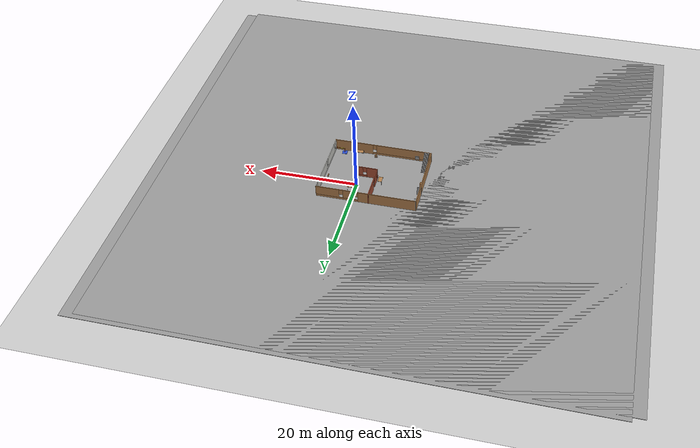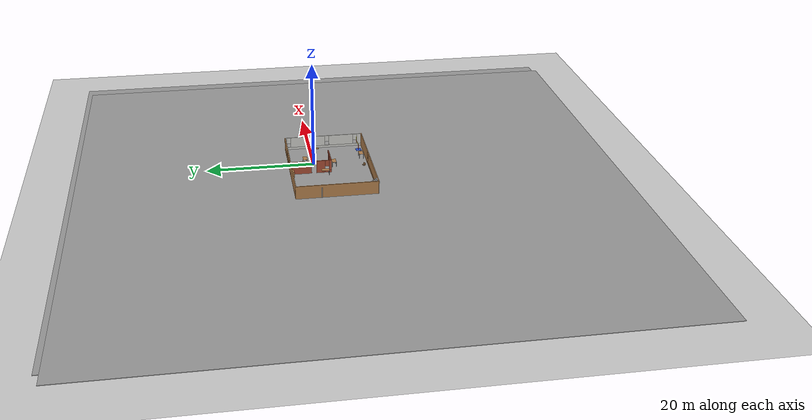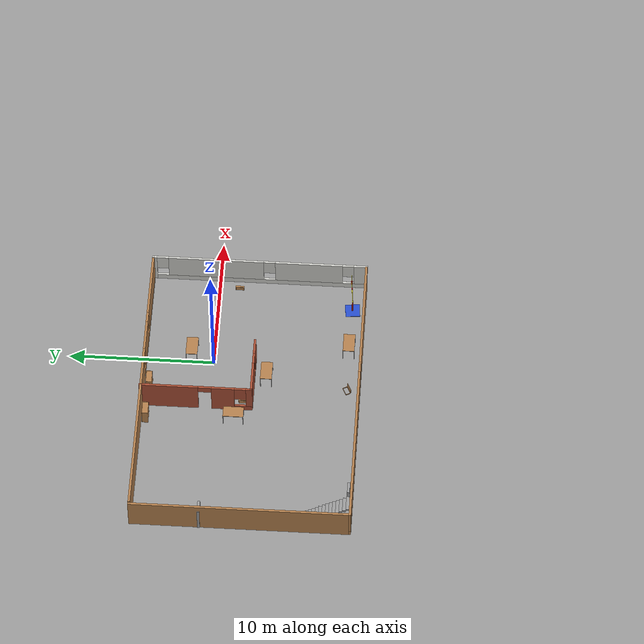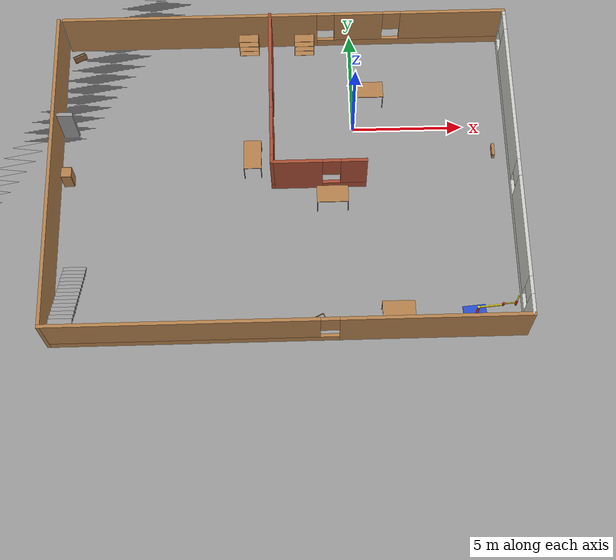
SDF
<sdf version="1.6">
 <world name="default">
  <light name="sun" type="directional">
   <pose>0 0 10 0 -0 0</pose>
   <diffuse>0.8 0.8 0.8 1</diffuse>
   <specular>0.1 0.1 0.1 1</specular>
   <attenuation>
    <range>1000</range>
    <constant>0.9</constant>
    <linear>0.01</linear>
    <quadratic>0.001</quadratic>
   </attenuation>
   <direction>-0.5 0.5 -1</direction>
  </light>
  <model name="ground_plane">
   <static>1</static>
   <link name="link">
    <collision name="collision">
     <geometry><plane><normal>0 0 1</normal><size>100 100</size></plane></geometry>
     <surface><friction><ode><mu>100</mu><mu2>50</mu2></ode></friction></surface>
    </collision>
    <visual name="visual">
     <cast_shadows>0</cast_shadows>
     <geometry><plane><normal>0 0 1</normal><size>100 100</size></plane></geometry>
     <material>
      <script><uri>file://media/materials/scripts/gazebo.material</uri><name>Gazebo/Grey</name></script>
     </material>
    </visual>
   </link>
  </model>
  <gravity>0 0 -9.8</gravity>
  <magnetic_field>6e-06 2.3e-05 -4.2e-05</magnetic_field>
  <atmosphere type="adiabatic"/>
  <physics name="default_physics" default="0" type="ode">
   <max_step_size>0.001</max_step_size>
   <real_time_factor>1</real_time_factor>
   <real_time_update_rate>1000</real_time_update_rate>
  </physics>
  <scene><ambient>0.4 0.4 0.4 1</ambient><background>0.7 0.7 0.7 1</background><shadows>1</shadows></scene>
  <spherical_coordinates>
   <surface_model>EARTH_WGS84</surface_model>
   <latitude_deg>0</latitude_deg>
   <longitude_deg>0</longitude_deg>
   <elevation>0</elevation>
   <heading_deg>0</heading_deg>
  </spherical_coordinates>
  <model name="map_my_world.world">
   <pose>-3.14852 -2.72011 0 0 -0 0</pose>
   <link name="Door_0">
    <collision name="Door_0_Collision">
     <geometry><box><size>0.9 0.17 2</size></box></geometry>
     <pose>0 0 1 0 -0 0</pose>
    </collision>
    <visual name="Door_0_Visual">
     <pose>0 0 1 0 -0 0</pose>
     <geometry><box><size>0.9 0.17 2</size></box></geometry>
     <material>
      <script><uri>file://media/materials/scripts/gazebo.material</uri><name>Gazebo/Grey</name></script>
     </material>
    </visual>
    <pose>-9.84195 2.74935 0 0 -0 0</pose>
   </link>
   <link name="Stairs_0">
    <visual name="Stairs_0_Visual_0">
     <pose>-9.28366 -3.99162 0.083333 0 -0 0</pose>
     <geometry><box><size>1 0.233333 0.166667</size></box></geometry>
     <material>
      <script><uri>file://media/materials/scripts/gazebo.material</uri><name>Gazebo/Grey</name></script>
      <ambient>1 1 1 1</ambient>
     </material>
    </visual>
    <collision name="Stairs_0_Collision_0">
     <geometry><box><size>1 0.233333 0.166667</size></box></geometry>
     <pose>-9.28366 -3.99162 0.083333 0 -0 0</pose>
    </collision>
    <visual name="Stairs_0_Visual_1">
     <pose>-9.28366 -4.22496 0.25 0 -0 0</pose>
     <geometry><box><size>1 0.233333 0.166667</size></box></geometry>
     <material>
      <script><uri>file://media/materials/scripts/gazebo.material</uri><name>Gazebo/Grey</name></script>
      <ambient>1 1 1 1</ambient>
     </material>
    </visual>
    <collision name="Stairs_0_Collision_1">
     <geometry><box><size>1 0.233333 0.166667</size></box></geometry>
     <pose>-9.28366 -4.22496 0.25 0 -0 0</pose>
    </collision>
    <visual name="Stairs_0_Visual_2">
     <pose>-9.28366 -4.45829 0.416667 0 -0 0</pose>
     <geometry><box><size>1 0.233333 0.166667</size></box></geometry>
     <material>
      <script><uri>file://media/materials/scripts/gazebo.material</uri><name>Gazebo/Grey</name></script>
      <ambient>1 1 1 1</ambient>
     </material>
    </visual>
    <collision name="Stairs_0_Collision_2">
     <geometry><box><size>1 0.233333 0.166667</size></box></geometry>
     <pose>-9.28366 -4.45829 0.416667 0 -0 0</pose>
    </collision>
    <visual name="Stairs_0_Visual_3">
     <pose>-9.28366 -4.69162 0.583333 0 -0 0</pose>
     <geometry><box><size>1 0.233333 0.166667</size></box></geometry>
     <material>
      <script><uri>file://media/materials/scripts/gazebo.material</uri><name>Gazebo/Grey</name></script>
      <ambient>1 1 1 1</ambient>
     </material>
    </visual>
    <collision name="Stairs_0_Collision_3">
     <geometry><box><size>1 0.233333 0.166667</size></box></geometry>
     <pose>-9.28366 -4.69162 0.583333 0 -0 0</pose>
    </collision>
    <visual name="Stairs_0_Visual_4">
     <pose>-9.28366 -4.92496 0.75 0 -0 0</pose>
     <geometry><box><size>1 0.233333 0.166667</size></box></geometry>
     <material>
      <script><uri>file://media/materials/scripts/gazebo.material</uri><name>Gazebo/Grey</name></script>
      <ambient>1 1 1 1</ambient>
     </material>
    </visual>
    <collision name="Stairs_0_Collision_4">
     <geometry><box><size>1 0.233333 0.166667</size></box></geometry>
     <pose>-9.28366 -4.92496 0.75 0 -0 0</pose>
    </collision>
    <visual name="Stairs_0_Visual_5">
     <pose>-9.28366 -5.15829 0.916667 0 -0 0</pose>
     <geometry><box><size>1 0.233333 0.166667</size></box></geometry>
     <material>
      <script><uri>file://media/materials/scripts/gazebo.material</uri><name>Gazebo/Grey</name></script>
      <ambient>1 1 1 1</ambient>
     </material>
    </visual>
    <collision name="Stairs_0_Collision_5">
     <geometry><box><size>1 0.233333 0.166667</size></box></geometry>
     <pose>-9.28366 -5.15829 0.916667 0 -0 0</pose>
    </collision>
    <visual name="Stairs_0_Visual_6">
     <pose>-9.28366 -5.39162 1.08333 0 -0 0</pose>
     <geometry><box><size>1 0.233333 0.166667</size></box></geometry>
     <material>
      <script><uri>file://media/materials/scripts/gazebo.material</uri><name>Gazebo/Grey</name></script>
      <ambient>1 1 1 1</ambient>
     </material>
    </visual>
    <collision name="Stairs_0_Collision_6">
     <geometry><box><size>1 0.233333 0.166667</size></box></geometry>
     <pose>-9.28366 -5.39162 1.08333 0 -0 0</pose>
    </collision>
    <visual name="Stairs_0_Visual_7">
     <pose>-9.28366 -5.62496 1.25 0 -0 0</pose>
     <geometry><box><size>1 0.233333 0.166667</size></box></geometry>
     <material>
      <script><uri>file://media/materials/scripts/gazebo.material</uri><name>Gazebo/Grey</name></script>
      <ambient>1 1 1 1</ambient>
     </material>
    </visual>
    <collision name="Stairs_0_Collision_7">
     <geometry><box><size>1 0.233333 0.166667</size></box></geometry>
     <pose>-9.28366 -5.62496 1.25 0 -0 0</pose>
    </collision>
    <visual name="Stairs_0_Visual_8">
     <pose>-9.28366 -5.85829 1.41667 0 -0 0</pose>
     <geometry><box><size>1 0.233333 0.166667</size></box></geometry>
     <material>
      <script><uri>file://media/materials/scripts/gazebo.material</uri><name>Gazebo/Grey</name></script>
      <ambient>1 1 1 1</ambient>
     </material>
    </visual>
    <collision name="Stairs_0_Collision_8">
     <geometry><box><size>1 0.233333 0.166667</size></box></geometry>
     <pose>-9.28366 -5.85829 1.41667 0 -0 0</pose>
    </collision>
    <visual name="Stairs_0_Visual_9">
     <pose>-9.28366 -6.09162 1.58333 0 -0 0</pose>
     <geometry><box><size>1 0.233333 0.166667</size></box></geometry>
     <material>
      <script><uri>file://media/materials/scripts/gazebo.material</uri><name>Gazebo/Grey</name></script>
      <ambient>1 1 1 1</ambient>
     </material>
    </visual>
    <collision name="Stairs_0_Collision_9">
     <geometry><box><size>1 0.233333 0.166667</size></box></geometry>
     <pose>-9.28366 -6.09162 1.58333 0 -0 0</pose>
    </collision>
    <visual name="Stairs_0_Visual_10">
     <pose>-9.28366 -6.32496 1.75 0 -0 0</pose>
     <geometry><box><size>1 0.233333 0.166667</size></box></geometry>
     <material>
      <script><uri>file://media/materials/scripts/gazebo.material</uri><name>Gazebo/Grey</name></script>
      <ambient>1 1 1 1</ambient>
     </material>
    </visual>
    <collision name="Stairs_0_Collision_10">
     <geometry><box><size>1 0.233333 0.166667</size></box></geometry>
     <pose>-9.28366 -6.32496 1.75 0 -0 0</pose>
    </collision>
    <visual name="Stairs_0_Visual_11">
     <pose>-9.28366 -6.55829 1.91667 0 -0 0</pose>
     <geometry><box><size>1 0.233333 0.166667</size></box></geometry>
     <material>
      <script><uri>file://media/materials/scripts/gazebo.material</uri><name>Gazebo/Grey</name></script>
      <ambient>1 1 1 1</ambient>
     </material>
    </visual>
    <collision name="Stairs_0_Collision_11">
     <geometry><box><size>1 0.233333 0.166667</size></box></geometry>
     <pose>-9.28366 -6.55829 1.91667 0 -0 0</pose>
    </collision>
    <visual name="Stairs_0_Visual_12">
     <pose>-9.28366 -6.79162 2.08333 0 -0 0</pose>
     <geometry><box><size>1 0.233333 0.166667</size></box></geometry>
     <material>
      <script><uri>file://media/materials/scripts/gazebo.material</uri><name>Gazebo/Grey</name></script>
      <ambient>1 1 1 1</ambient>
     </material>
    </visual>
    <collision name="Stairs_0_Collision_12">
     <geometry><box><size>1 0.233333 0.166667</size></box></geometry>
     <pose>-9.28366 -6.79162 2.08333 0 -0 0</pose>
    </collision>
    <visual name="Stairs_0_Visual_13">
     <pose>-9.28366 -7.02496 2.25 0 -0 0</pose>
     <geometry><box><size>1 0.233333 0.166667</size></box></geometry>
     <material>
      <script><uri>file://media/materials/scripts/gazebo.material</uri><name>Gazebo/Grey</name></script>
      <ambient>1 1 1 1</ambient>
     </material>
    </visual>
    <collision name="Stairs_0_Collision_13">
     <geometry><box><size>1 0.233333 0.166667</size></box></geometry>
     <pose>-9.28366 -7.02496 2.25 0 -0 0</pose>
    </collision>
    <visual name="Stairs_0_Visual_14">
     <pose>-9.28366 -7.25829 2.41667 0 -0 0</pose>
     <geometry><box><size>1 0.233333 0.166667</size></box></geometry>
     <material>
      <script><uri>file://media/materials/scripts/gazebo.material</uri><name>Gazebo/Grey</name></script>
      <ambient>1 1 1 1</ambient>
     </material>
    </visual>
    <collision name="Stairs_0_Collision_14">
     <geometry><box><size>1 0.233333 0.166667</size></box></geometry>
     <pose>-9.28366 -7.25829 2.41667 0 -0 0</pose>
    </collision>
   </link>
   <link name="Wall_11">
    <pose>0.115 7.40174 0 0 -0 0</pose>
    <visual name="Wall_11_Visual_0">
     <pose>-4.30918 0 1.25 0 -0 0</pose>
     <geometry><box><size>11.6316 0.15 2.5</size></box></geometry>
     <material>
      <script><uri>file://media/materials/scripts/gazebo.material</uri><name>Gazebo/Wood</name></script>
      <ambient>0.435294 0.796078 0.67451 1</ambient>
     </material>
    </visual>
    <collision name="Wall_11_Collision_0">
     <geometry><box><size>11.6316 0.15 2.5</size></box></geometry>
     <pose>-4.30918 0 1.25 0 -0 0</pose>
    </collision>
    <visual name="Wall_11_Visual_1">
     <pose>5.81582 0 0.25 0 -0 0</pose>
     <geometry><box><size>8.61835 0.15 0.5</size></box></geometry>
     <material>
      <script><uri>file://media/materials/scripts/gazebo.material</uri><name>Gazebo/Wood</name></script>
      <ambient>0.435294 0.796078 0.67451 1</ambient>
     </material>
    </visual>
    <collision name="Wall_11_Collision_1">
     <geometry><box><size>8.61835 0.15 0.5</size></box></geometry>
     <pose>5.81582 0 0.25 0 -0 0</pose>
    </collision>
    <visual name="Wall_11_Visual_2">
     <pose>3.41867 0 1.5 0 -0 0</pose>
     <geometry><box><size>2.22405 0.15 2</size></box></geometry>
     <material>
      <script><uri>file://media/materials/scripts/gazebo.material</uri><name>Gazebo/Wood</name></script>
      <ambient>0.435294 0.796078 0.67451 1</ambient>
     </material>
    </visual>
    <collision name="Wall_11_Collision_2">
     <geometry><box><size>2.22405 0.15 2</size></box></geometry>
     <pose>3.41867 0 1.5 0 -0 0</pose>
    </collision>
    <visual name="Wall_11_Visual_3">
     <pose>7.72785 0 1.5 0 -0 0</pose>
     <geometry><box><size>4.7943 0.15 2</size></box></geometry>
     <material>
      <script><uri>file://media/materials/scripts/gazebo.material</uri><name>Gazebo/Wood</name></script>
      <ambient>0.435294 0.796078 0.67451 1</ambient>
     </material>
    </visual>
    <collision name="Wall_11_Collision_3">
     <geometry><box><size>4.7943 0.15 2</size></box></geometry>
     <pose>7.72785 0 1.5 0 -0 0</pose>
    </collision>
    <visual name="Wall_11_Visual_4">
     <pose>1.90665 0 1.9 0 -0 0</pose>
     <geometry><box><size>0.8 0.15 1.2</size></box></geometry>
     <material>
      <script><uri>file://media/materials/scripts/gazebo.material</uri><name>Gazebo/Wood</name></script>
      <ambient>0.435294 0.796078 0.67451 1</ambient>
     </material>
    </visual>
    <collision name="Wall_11_Collision_4">
     <geometry><box><size>0.8 0.15 1.2</size></box></geometry>
     <pose>1.90665 0 1.9 0 -0 0</pose>
    </collision>
    <visual name="Wall_11_Visual_5">
     <pose>4.9307 0 1.9 0 -0 0</pose>
     <geometry><box><size>0.8 0.15 1.2</size></box></geometry>
     <material>
      <script><uri>file://media/materials/scripts/gazebo.material</uri><name>Gazebo/Wood</name></script>
      <ambient>0.435294 0.796078 0.67451 1</ambient>
     </material>
    </visual>
    <collision name="Wall_11_Collision_5">
     <geometry><box><size>0.8 0.15 1.2</size></box></geometry>
     <pose>4.9307 0 1.9 0 -0 0</pose>
    </collision>
   </link>
   <link name="Wall_12">
    <collision name="Wall_12_Collision">
     <geometry><box><size>0.16 0.15 2.5</size></box></geometry>
     <pose>0 0 1.25 0 -0 0</pose>
    </collision>
    <visual name="Wall_12_Visual">
     <pose>0 0 1.25 0 -0 0</pose>
     <geometry><box><size>0.16 0.15 2.5</size></box></geometry>
     <material>
      <script><uri>file://media/materials/scripts/gazebo.material</uri><name>Gazebo/Grey</name></script>
      <ambient>1 1 1 1</ambient>
     </material>
    </visual>
    <pose>10.17 7.40174 0 0 -0 0</pose>
   </link>
   <link name="Wall_13">
    <pose>10.175 -0.023262 0 0 0 -1.5708</pose>
    <visual name="Wall_13_Visual_0">
     <pose>-7.33683 0 1.25 0 -0 0</pose>
     <geometry><box><size>0.326335 0.15 2.5</size></box></geometry>
     <material>
      <script><uri>file://media/materials/scripts/gazebo.material</uri><name>Gazebo/CeilingTiled</name></script>
      <ambient>1 1 1 1</ambient>
     </material>
    </visual>
    <collision name="Wall_13_Collision_0">
     <geometry><box><size>0.326335 0.15 2.5</size></box></geometry>
     <pose>-7.33683 0 1.25 0 -0 0</pose>
    </collision>
    <visual name="Wall_13_Visual_1">
     <pose>0.163168 0 0.25 0 -0 0</pose>
     <geometry><box><size>14.6737 0.15 0.5</size></box></geometry>
     <material>
      <script><uri>file://media/materials/scripts/gazebo.material</uri><name>Gazebo/CeilingTiled</name></script>
      <ambient>1 1 1 1</ambient>
     </material>
    </visual>
    <collision name="Wall_13_Collision_1">
     <geometry><box><size>14.6737 0.15 0.5</size></box></geometry>
     <pose>0.163168 0 0.25 0 -0 0</pose>
    </collision>
    <visual name="Wall_13_Visual_2">
     <pose>-3.05175 0 1.5 0 -0 0</pose>
     <geometry><box><size>6.64383 0.15 2</size></box></geometry>
     <material>
      <script><uri>file://media/materials/scripts/gazebo.material</uri><name>Gazebo/CeilingTiled</name></script>
      <ambient>1 1 1 1</ambient>
     </material>
    </visual>
    <collision name="Wall_13_Collision_2">
     <geometry><box><size>6.64383 0.15 2</size></box></geometry>
     <pose>-3.05175 0 1.5 0 -0 0</pose>
    </collision>
    <visual name="Wall_13_Visual_3">
     <pose>3.41507 0 1.5 0 -0 0</pose>
     <geometry><box><size>4.68982 0.15 2</size></box></geometry>
     <material>
      <script><uri>file://media/materials/scripts/gazebo.material</uri><name>Gazebo/CeilingTiled</name></script>
      <ambient>1 1 1 1</ambient>
     </material>
    </visual>
    <collision name="Wall_13_Collision_3">
     <geometry><box><size>4.68982 0.15 2</size></box></geometry>
     <pose>3.41507 0 1.5 0 -0 0</pose>
    </collision>
    <visual name="Wall_13_Visual_4">
     <pose>7.02999 0 1.5 0 -0 0</pose>
     <geometry><box><size>0.940017 0.15 2</size></box></geometry>
     <material>
      <script><uri>file://media/materials/scripts/gazebo.material</uri><name>Gazebo/CeilingTiled</name></script>
      <ambient>1 1 1 1</ambient>
     </material>
    </visual>
    <collision name="Wall_13_Collision_4">
     <geometry><box><size>0.940017 0.15 2</size></box></geometry>
     <pose>7.02999 0 1.5 0 -0 0</pose>
    </collision>
    <visual name="Wall_13_Visual_5">
     <pose>-6.77367 0 1.9 0 -0 0</pose>
     <geometry><box><size>0.8 0.15 1.2</size></box></geometry>
     <material>
      <script><uri>file://media/materials/scripts/gazebo.material</uri><name>Gazebo/CeilingTiled</name></script>
      <ambient>1 1 1 1</ambient>
     </material>
    </visual>
    <collision name="Wall_13_Collision_5">
     <geometry><box><size>0.8 0.15 1.2</size></box></geometry>
     <pose>-6.77367 0 1.9 0 -0 0</pose>
    </collision>
    <visual name="Wall_13_Visual_6">
     <pose>0.670161 0 1.9 0 -0 0</pose>
     <geometry><box><size>0.8 0.15 1.2</size></box></geometry>
     <material>
      <script><uri>file://media/materials/scripts/gazebo.material</uri><name>Gazebo/CeilingTiled</name></script>
      <ambient>1 1 1 1</ambient>
     </material>
    </visual>
    <collision name="Wall_13_Collision_6">
     <geometry><box><size>0.8 0.15 1.2</size></box></geometry>
     <pose>0.670161 0 1.9 0 -0 0</pose>
    </collision>
    <visual name="Wall_13_Visual_7">
     <pose>6.15998 0 1.9 0 -0 0</pose>
     <geometry><box><size>0.8 0.15 1.2</size></box></geometry>
     <material>
      <script><uri>file://media/materials/scripts/gazebo.material</uri><name>Gazebo/CeilingTiled</name></script>
      <ambient>1 1 1 1</ambient>
     </material>
    </visual>
    <collision name="Wall_13_Collision_7">
     <geometry><box><size>0.8 0.15 1.2</size></box></geometry>
     <pose>6.15998 0 1.9 0 -0 0</pose>
    </collision>
   </link>
   <link name="Wall_14">
    <pose>0 -7.44826 0 0 -0 3.14159</pose>
    <visual name="Wall_14_Visual_0">
     <pose>-6.21951 0 1.25 0 -0 0</pose>
     <geometry><box><size>8.06097 0.15 2.5</size></box></geometry>
     <material>
      <script><uri>file://media/materials/scripts/gazebo.material</uri><name>Gazebo/Wood</name></script>
      <ambient>1 1 1 1</ambient>
     </material>
    </visual>
    <collision name="Wall_14_Collision_0">
     <geometry><box><size>8.06097 0.15 2.5</size></box></geometry>
     <pose>-6.21951 0 1.25 0 -0 0</pose>
    </collision>
    <visual name="Wall_14_Visual_1">
     <pose>4.03049 0 0.25 0 -0 0</pose>
     <geometry><box><size>12.439 0.15 0.5</size></box></geometry>
     <material>
      <script><uri>file://media/materials/scripts/gazebo.material</uri><name>Gazebo/Wood</name></script>
      <ambient>1 1 1 1</ambient>
     </material>
    </visual>
    <collision name="Wall_14_Collision_1">
     <geometry><box><size>12.439 0.15 0.5</size></box></geometry>
     <pose>4.03049 0 0.25 0 -0 0</pose>
    </collision>
    <visual name="Wall_14_Visual_2">
     <pose>4.43049 0 1.5 0 -0 0</pose>
     <geometry><box><size>11.639 0.15 2</size></box></geometry>
     <material>
      <script><uri>file://media/materials/scripts/gazebo.material</uri><name>Gazebo/Wood</name></script>
      <ambient>1 1 1 1</ambient>
     </material>
    </visual>
    <collision name="Wall_14_Collision_2">
     <geometry><box><size>11.639 0.15 2</size></box></geometry>
     <pose>4.43049 0 1.5 0 -0 0</pose>
    </collision>
    <visual name="Wall_14_Visual_3">
     <pose>-1.78903 0 1.9 0 -0 0</pose>
     <geometry><box><size>0.8 0.15 1.2</size></box></geometry>
     <material>
      <script><uri>file://media/materials/scripts/gazebo.material</uri><name>Gazebo/Wood</name></script>
      <ambient>1 1 1 1</ambient>
     </material>
    </visual>
    <collision name="Wall_14_Collision_3">
     <geometry><box><size>0.8 0.15 1.2</size></box></geometry>
     <pose>-1.78903 0 1.9 0 -0 0</pose>
    </collision>
   </link>
   <link name="Wall_15">
    <collision name="Wall_15_Collision">
     <geometry><box><size>15 0.15 2.5</size></box></geometry>
     <pose>0 0 1.25 0 -0 0</pose>
    </collision>
    <visual name="Wall_15_Visual">
     <pose>0 0 1.25 0 -0 0</pose>
     <geometry><box><size>15 0.15 2.5</size></box></geometry>
     <material>
      <script><uri>file://media/materials/scripts/gazebo.material</uri><name>Gazebo/Wood</name></script>
      <ambient>0.435294 0.796078 0.67451 1</ambient>
     </material>
    </visual>
    <pose>-10.175 -0.023262 0 0 -0 1.5708</pose>
   </link>
   <link name="Wall_17">
    <pose>-0.537169 3.64826 0 0 0 -1.5708</pose>
    <visual name="Wall_17_Visual_0">
     <pose>-1.85261 0 1.25 0 -0 0</pose>
     <geometry><box><size>4.04477 0.15 2.5</size></box></geometry>
     <material>
      <script><uri>file://media/materials/scripts/gazebo.material</uri><name>Gazebo/Bricks</name></script>
      <ambient>1 1 1 1</ambient>
     </material>
    </visual>
    <collision name="Wall_17_Collision_0">
     <geometry><box><size>4.04477 0.15 2.5</size></box></geometry>
     <pose>-1.85261 0 1.25 0 -0 0</pose>
    </collision>
    <visual name="Wall_17_Visual_1">
     <pose>1.85439 0 1.25 0 -0 0</pose>
     <geometry><box><size>1.56924 0.15 2.5</size></box></geometry>
     <material>
      <script><uri>file://media/materials/scripts/gazebo.material</uri><name>Gazebo/Bricks</name></script>
      <ambient>1 1 1 1</ambient>
     </material>
    </visual>
    <collision name="Wall_17_Collision_1">
     <geometry><box><size>1.56924 0.15 2.5</size></box></geometry>
     <pose>1.85439 0 1.25 0 -0 0</pose>
    </collision>
    <visual name="Wall_17_Visual_2">
     <pose>3.25701 0 0.25 0 -0 0</pose>
     <geometry><box><size>1.23598 0.15 0.5</size></box></geometry>
     <material>
      <script><uri>file://media/materials/scripts/gazebo.material</uri><name>Gazebo/Bricks</name></script>
      <ambient>1 1 1 1</ambient>
     </material>
    </visual>
    <collision name="Wall_17_Collision_2">
     <geometry><box><size>1.23598 0.15 0.5</size></box></geometry>
     <pose>3.25701 0 0.25 0 -0 0</pose>
    </collision>
    <visual name="Wall_17_Visual_3">
     <pose>3.65701 0 1.5 0 -0 0</pose>
     <geometry><box><size>0.435985 0.15 2</size></box></geometry>
     <material>
      <script><uri>file://media/materials/scripts/gazebo.material</uri><name>Gazebo/Bricks</name></script>
      <ambient>1 1 1 1</ambient>
     </material>
    </visual>
    <collision name="Wall_17_Collision_3">
     <geometry><box><size>0.435985 0.15 2</size></box></geometry>
     <pose>3.65701 0 1.5 0 -0 0</pose>
    </collision>
    <visual name="Wall_17_Visual_4">
     <pose>3.03902 0 1.9 0 -0 0</pose>
     <geometry><box><size>0.8 0.15 1.2</size></box></geometry>
     <material>
      <script><uri>file://media/materials/scripts/gazebo.material</uri><name>Gazebo/Bricks</name></script>
      <ambient>1 1 1 1</ambient>
     </material>
    </visual>
    <collision name="Wall_17_Collision_4">
     <geometry><box><size>0.8 0.15 1.2</size></box></geometry>
     <pose>3.03902 0 1.9 0 -0 0</pose>
    </collision>
    <visual name="Wall_17_Visual_5">
     <pose>0.619772 0 2.25 0 -0 0</pose>
     <geometry><box><size>0.9 0.15 0.5</size></box></geometry>
     <material>
      <script><uri>file://media/materials/scripts/gazebo.material</uri><name>Gazebo/Bricks</name></script>
      <ambient>1 1 1 1</ambient>
     </material>
    </visual>
    <collision name="Wall_17_Collision_5">
     <geometry><box><size>0.9 0.15 0.5</size></box></geometry>
     <pose>0.619772 0 2.25 0 -0 0</pose>
    </collision>
   </link>
   <link name="Wall_18">
    <pose>1.51283 -0.151738 0 0 -0 0</pose>
    <visual name="Wall_18_Visual_0">
     <pose>-0.98483 0 1.25 0 -0 0</pose>
     <geometry><box><size>2.28034 0.15 2.5</size></box></geometry>
     <material>
      <script><uri>file://media/materials/scripts/gazebo.material</uri><name>Gazebo/Bricks</name></script>
      <ambient>1 1 1 1</ambient>
     </material>
    </visual>
    <collision name="Wall_18_Collision_0">
     <geometry><box><size>2.28034 0.15 2.5</size></box></geometry>
     <pose>-0.98483 0 1.25 0 -0 0</pose>
    </collision>
    <visual name="Wall_18_Visual_1">
     <pose>1.14017 0 0.25 0 -0 0</pose>
     <geometry><box><size>1.96966 0.15 0.5</size></box></geometry>
     <material>
      <script><uri>file://media/materials/scripts/gazebo.material</uri><name>Gazebo/Bricks</name></script>
      <ambient>1 1 1 1</ambient>
     </material>
    </visual>
    <collision name="Wall_18_Collision_1">
     <geometry><box><size>1.96966 0.15 0.5</size></box></geometry>
     <pose>1.14017 0 0.25 0 -0 0</pose>
    </collision>
    <visual name="Wall_18_Visual_2">
     <pose>1.54017 0 1.5 0 -0 0</pose>
     <geometry><box><size>1.16966 0.15 2</size></box></geometry>
     <material>
      <script><uri>file://media/materials/scripts/gazebo.material</uri><name>Gazebo/Bricks</name></script>
      <ambient>1 1 1 1</ambient>
     </material>
    </visual>
    <collision name="Wall_18_Collision_2">
     <geometry><box><size>1.16966 0.15 2</size></box></geometry>
     <pose>1.54017 0 1.5 0 -0 0</pose>
    </collision>
    <visual name="Wall_18_Visual_3">
     <pose>0.555339 0 1.9 0 -0 0</pose>
     <geometry><box><size>0.8 0.15 1.2</size></box></geometry>
     <material>
      <script><uri>file://media/materials/scripts/gazebo.material</uri><name>Gazebo/Bricks</name></script>
      <ambient>1 1 1 1</ambient>
     </material>
    </visual>
    <collision name="Wall_18_Collision_3">
     <geometry><box><size>0.8 0.15 1.2</size></box></geometry>
     <pose>0.555339 0 1.9 0 -0 0</pose>
    </collision>
   </link>
   <link name="Window_1">
    <collision name="Window_1_Collision">
     <geometry><box><size>0.8 0.17 0.8</size></box></geometry>
     <pose>0 0 0.4 0 -0 0</pose>
    </collision>
    <visual name="Window_1_Visual">
     <pose>0 0 0.4 0 -0 0</pose>
     <geometry><box><size>0.8 0.17 0.8</size></box></geometry>
     <material>
      <script><uri>file://media/materials/scripts/gazebo.material</uri><name>Gazebo/Grey</name></script>
     </material>
    </visual>
    <pose>-7.28314 -7.20677 0.5 0 -0 0</pose>
   </link>
   <static>1</static>
  </model>
  <model name="cabinet">
   <static>1</static>
   <link name="cabinet_bottom_plate">
    <inertial>
     <pose>0 0 -1 0 -0 0</pose>
     <inertia><ixx>2.05</ixx><ixy>0</ixy><ixz>0</ixz><iyy>2.05</iyy><iyz>0</iyz><izz>2.05</izz></inertia>
     <mass>25</mass>
    </inertial>
    <collision name="cabinet_bottom_plate_geom">
     <pose>0 0 0.01 0 -0 0</pose>
     <geometry><box><size>0.45 0.45 0.02</size></box></geometry>
    </collision>
    <visual name="cabinet_bottom_plate_geom_visual">
     <pose>0 0 0.01 0 -0 0</pose>
     <geometry><box><size>0.45 0.45 0.02</size></box></geometry>
     <material>
      <script><uri>file://media/materials/scripts/gazebo.material</uri><name>Gazebo/Wood</name></script>
     </material>
    </visual>
    <collision name="cabinet_bottom_plate_geom_cabinet_back_plate">
     <pose>0.235 0 0.51 0 -0 0</pose>
     <geometry><box><size>0.02 0.45 1.02</size></box></geometry>
    </collision>
    <visual name="cabinet_bottom_plate_geom_cabinet_back_plate_visual">
     <pose>0.235 0 0.51 0 -0 0</pose>
     <geometry><box><size>0.02 0.45 1.02</size></box></geometry>
     <material>
      <script><uri>file://media/materials/scripts/gazebo.material</uri><name>Gazebo/Wood</name></script>
     </material>
    </visual>
    <collision name="cabinet_bottom_plate_geom_cabinet_left_plate">
     <pose>0 0.235 0.51 0 -0 0</pose>
     <geometry><box><size>0.45 0.02 1.02</size></box></geometry>
    </collision>
    <visual name="cabinet_bottom_plate_geom_cabinet_left_plate_visual">
     <pose>0 0.235 0.51 0 -0 0</pose>
     <geometry><box><size>0.45 0.02 1.02</size></box></geometry>
     <material>
      <script><uri>file://media/materials/scripts/gazebo.material</uri><name>Gazebo/Wood</name></script>
     </material>
    </visual>
    <collision name="cabinet_bottom_plate_geom_cabinet_middle_plate">
     <pose>0 0 0.51 0 -0 0</pose>
     <geometry><box><size>0.45 0.45 0.02</size></box></geometry>
    </collision>
    <visual name="cabinet_bottom_plate_geom_cabinet_middle_plate_visual">
     <pose>0 0 0.51 0 -0 0</pose>
     <geometry><box><size>0.45 0.45 0.02</size></box></geometry>
     <material>
      <script><uri>file://media/materials/scripts/gazebo.material</uri><name>Gazebo/Wood</name></script>
     </material>
    </visual>
    <collision name="cabinet_bottom_plate_geom_cabinet_right_plate">
     <pose>0 -0.235 0.51 0 -0 0</pose>
     <geometry><box><size>0.45 0.02 1.02</size></box></geometry>
    </collision>
    <visual name="cabinet_bottom_plate_geom_cabinet_right_plate_visual">
     <pose>0 -0.235 0.51 0 -0 0</pose>
     <geometry><box><size>0.45 0.02 1.02</size></box></geometry>
     <material>
      <script><uri>file://media/materials/scripts/gazebo.material</uri><name>Gazebo/Wood</name></script>
     </material>
    </visual>
    <collision name="cabinet_bottom_plate_geom_cabinet_top_plate">
     <pose>0 0 1.01 0 -0 0</pose>
     <geometry><box><size>0.45 0.45 0.02</size></box></geometry>
    </collision>
    <visual name="cabinet_bottom_plate_geom_cabinet_top_plate_visual">
     <pose>0 0 1.01 0 -0 0</pose>
     <geometry><box><size>0.45 0.45 0.02</size></box></geometry>
     <material>
      <script><uri>file://media/materials/scripts/gazebo.material</uri><name>Gazebo/Wood</name></script>
     </material>
    </visual>
   </link>
   <pose>-12.8791 -2.34771 0 0 -0 0</pose>
  </model>
  <model name="bookshelf">
   <static>1</static>
   <link name="link">
    <inertial><mass>1</mass></inertial>
    <collision name="back">
     <pose>0 0.005 0.6 0 -0 0</pose>
     <geometry><box><size>0.9 0.01 1.2</size></box></geometry>
    </collision>
    <visual name="visual1">
     <pose>0 0.005 0.6 0 -0 0</pose>
     <geometry><box><size>0.9 0.01 1.2</size></box></geometry>
     <material>
      <script><uri>file://media/materials/scripts/gazebo.material</uri><name>Gazebo/Wood</name></script>
     </material>
    </visual>
    <collision name="left_side">
     <pose>0.45 -0.195 0.6 0 -0 0</pose>
     <geometry><box><size>0.02 0.4 1.2</size></box></geometry>
    </collision>
    <visual name="visual2">
     <pose>0.45 -0.195 0.6 0 -0 0</pose>
     <geometry><box><size>0.02 0.4 1.2</size></box></geometry>
     <material>
      <script><uri>file://media/materials/scripts/gazebo.material</uri><name>Gazebo/Wood</name></script>
     </material>
    </visual>
    <collision name="right_side">
     <pose>-0.45 -0.195 0.6 0 -0 0</pose>
     <geometry><box><size>0.02 0.4 1.2</size></box></geometry>
    </collision>
    <visual name="visual3">
     <pose>-0.45 -0.195 0.6 0 -0 0</pose>
     <geometry><box><size>0.02 0.4 1.2</size></box></geometry>
     <material>
      <script><uri>file://media/materials/scripts/gazebo.material</uri><name>Gazebo/Wood</name></script>
     </material>
    </visual>
    <collision name="bottom">
     <pose>0 -0.195 0.03 0 -0 0</pose>
     <geometry><box><size>0.88 0.4 0.06</size></box></geometry>
    </collision>
    <visual name="visual4">
     <pose>0 -0.195 0.03 0 -0 0</pose>
     <geometry><box><size>0.88 0.4 0.06</size></box></geometry>
     <material>
      <script><uri>file://media/materials/scripts/gazebo.material</uri><name>Gazebo/Wood</name></script>
     </material>
    </visual>
    <collision name="top">
     <pose>0 -0.195 1.19 0 -0 0</pose>
     <geometry><box><size>0.88 0.4 0.02</size></box></geometry>
    </collision>
    <visual name="visual5">
     <pose>0 -0.195 1.19 0 -0 0</pose>
     <geometry><box><size>0.88 0.4 0.02</size></box></geometry>
     <material>
      <script><uri>file://media/materials/scripts/gazebo.material</uri><name>Gazebo/Wood</name></script>
     </material>
    </visual>
    <collision name="low_shelf">
     <pose>0 -0.195 0.43 0 -0 0</pose>
     <geometry><box><size>0.88 0.4 0.02</size></box></geometry>
    </collision>
    <visual name="visual6">
     <pose>0 -0.195 0.43 0 -0 0</pose>
     <geometry><box><size>0.88 0.4 0.02</size></box></geometry>
     <material>
      <script><uri>file://media/materials/scripts/gazebo.material</uri><name>Gazebo/Wood</name></script>
     </material>
    </visual>
    <collision name="high_shelf">
     <pose>0 -0.195 0.8 0 -0 0</pose>
     <geometry><box><size>0.88 0.4 0.02</size></box></geometry>
    </collision>
    <visual name="visual7">
     <pose>0 -0.195 0.8 0 -0 0</pose>
     <geometry><box><size>0.88 0.4 0.02</size></box></geometry>
     <material>
      <script><uri>file://media/materials/scripts/gazebo.material</uri><name>Gazebo/Wood</name></script>
     </material>
    </visual>
   </link>
   <pose>-4.71155 4.52272 0 0 -0 0</pose>
  </model>
  <model name="bookshelf_0">
   <static>1</static>
   <link name="link">
    <inertial><mass>1</mass></inertial>
    <collision name="back">
     <pose>0 0.005 0.6 0 -0 0</pose>
     <geometry><box><size>0.9 0.01 1.2</size></box></geometry>
    </collision>
    <visual name="visual1">
     <pose>0 0.005 0.6 0 -0 0</pose>
     <geometry><box><size>0.9 0.01 1.2</size></box></geometry>
     <material>
      <script><uri>file://media/materials/scripts/gazebo.material</uri><name>Gazebo/Wood</name></script>
     </material>
    </visual>
    <collision name="left_side">
     <pose>0.45 -0.195 0.6 0 -0 0</pose>
     <geometry><box><size>0.02 0.4 1.2</size></box></geometry>
    </collision>
    <visual name="visual2">
     <pose>0.45 -0.195 0.6 0 -0 0</pose>
     <geometry><box><size>0.02 0.4 1.2</size></box></geometry>
     <material>
      <script><uri>file://media/materials/scripts/gazebo.material</uri><name>Gazebo/Wood</name></script>
     </material>
    </visual>
    <collision name="right_side">
     <pose>-0.45 -0.195 0.6 0 -0 0</pose>
     <geometry><box><size>0.02 0.4 1.2</size></box></geometry>
    </collision>
    <visual name="visual3">
     <pose>-0.45 -0.195 0.6 0 -0 0</pose>
     <geometry><box><size>0.02 0.4 1.2</size></box></geometry>
     <material>
      <script><uri>file://media/materials/scripts/gazebo.material</uri><name>Gazebo/Wood</name></script>
     </material>
    </visual>
    <collision name="bottom">
     <pose>0 -0.195 0.03 0 -0 0</pose>
     <geometry><box><size>0.88 0.4 0.06</size></box></geometry>
    </collision>
    <visual name="visual4">
     <pose>0 -0.195 0.03 0 -0 0</pose>
     <geometry><box><size>0.88 0.4 0.06</size></box></geometry>
     <material>
      <script><uri>file://media/materials/scripts/gazebo.material</uri><name>Gazebo/Wood</name></script>
     </material>
    </visual>
    <collision name="top">
     <pose>0 -0.195 1.19 0 -0 0</pose>
     <geometry><box><size>0.88 0.4 0.02</size></box></geometry>
    </collision>
    <visual name="visual5">
     <pose>0 -0.195 1.19 0 -0 0</pose>
     <geometry><box><size>0.88 0.4 0.02</size></box></geometry>
     <material>
      <script><uri>file://media/materials/scripts/gazebo.material</uri><name>Gazebo/Wood</name></script>
     </material>
    </visual>
    <collision name="low_shelf">
     <pose>0 -0.195 0.43 0 -0 0</pose>
     <geometry><box><size>0.88 0.4 0.02</size></box></geometry>
    </collision>
    <visual name="visual6">
     <pose>0 -0.195 0.43 0 -0 0</pose>
     <geometry><box><size>0.88 0.4 0.02</size></box></geometry>
     <material>
      <script><uri>file://media/materials/scripts/gazebo.material</uri><name>Gazebo/Wood</name></script>
     </material>
    </visual>
    <collision name="high_shelf">
     <pose>0 -0.195 0.8 0 -0 0</pose>
     <geometry><box><size>0.88 0.4 0.02</size></box></geometry>
    </collision>
    <visual name="visual7">
     <pose>0 -0.195 0.8 0 -0 0</pose>
     <geometry><box><size>0.88 0.4 0.02</size></box></geometry>
     <material>
      <script><uri>file://media/materials/scripts/gazebo.material</uri><name>Gazebo/Wood</name></script>
     </material>
    </visual>
   </link>
   <pose>-2.13399 4.47247 0 0 -0 0</pose>
  </model>
  <model name="ground_plane_0">
   <static>1</static>
   <link name="link">
    <collision name="collision">
     <geometry><plane><normal>0 0 1</normal><size>100 100</size></plane></geometry>
     <surface><friction><ode><mu>100</mu><mu2>50</mu2></ode></friction></surface>
    </collision>
    <visual name="visual">
     <cast_shadows>0</cast_shadows>
     <geometry><plane><normal>0 0 1</normal><size>100 100</size></plane></geometry>
     <material>
      <script><uri>file://media/materials/scripts/gazebo.material</uri><name>Gazebo/Grey</name></script>
     </material>
    </visual>
   </link>
   <pose>-9.60054 -6.20571 0 0 -0 0</pose>
  </model>
  <model name="ground_plane_1">
   <static>1</static>
   <link name="link">
    <collision name="collision">
     <geometry><plane><normal>0 0 1</normal><size>100 100</size></plane></geometry>
     <surface><friction><ode><mu>100</mu><mu2>50</mu2></ode></friction></surface>
    </collision>
    <visual name="visual">
     <cast_shadows>0</cast_shadows>
     <geometry><plane><normal>0 0 1</normal><size>100 100</size></plane></geometry>
     <material>
      <script><uri>file://media/materials/scripts/gazebo.material</uri><name>Gazebo/Grey</name></script>
     </material>
    </visual>
   </link>
   <pose>-7.29819 -5.30691 0 0 -0 0</pose>
  </model>
  <model name="table">
   <static>0</static>
   <link name="link">
    <collision name="surface">
     <pose>0 0 1 0 -0 0</pose>
     <geometry><box><size>1.5 0.8 0.03</size></box></geometry>
     <surface><friction><ode><mu>0.6</mu><mu2>0.6</mu2></ode></friction></surface>
    </collision>
    <visual name="visual1">
     <pose>0 0 1 0 -0 0</pose>
     <geometry><box><size>1.4 0.8 0.04</size></box></geometry>
     <material>
      <script><uri>file://media/materials/scripts/gazebo.material</uri><name>Gazebo/Wood</name></script>
     </material>
    </visual>
    <collision name="front_left_leg">
     <pose>0.68 0.38 0.5 0 -0 0</pose>
     <geometry><cylinder><radius>0.02</radius><length>1</length></cylinder></geometry>
    </collision>
    <visual name="front_left_leg">
     <pose>0.68 0.38 0.5 0 -0 0</pose>
     <geometry><cylinder><radius>0.02</radius><length>1</length></cylinder></geometry>
     <material>
      <script><uri>file://media/materials/scripts/gazebo.material</uri><name>Gazebo/Grey</name></script>
     </material>
    </visual>
    <collision name="front_right_leg">
     <pose>0.68 -0.38 0.5 0 -0 0</pose>
     <geometry><cylinder><radius>0.02</radius><length>1</length></cylinder></geometry>
    </collision>
    <visual name="front_right_leg">
     <pose>0.68 -0.38 0.5 0 -0 0</pose>
     <geometry><cylinder><radius>0.02</radius><length>1</length></cylinder></geometry>
     <material>
      <script><uri>file://media/materials/scripts/gazebo.material</uri><name>Gazebo/Grey</name></script>
     </material>
    </visual>
    <collision name="back_right_leg">
     <pose>-0.68 -0.38 0.5 0 -0 0</pose>
     <geometry><cylinder><radius>0.02</radius><length>1</length></cylinder></geometry>
    </collision>
    <visual name="back_right_leg">
     <pose>-0.68 -0.38 0.5 0 -0 0</pose>
     <geometry><cylinder><radius>0.02</radius><length>1</length></cylinder></geometry>
     <material>
      <script><uri>file://media/materials/scripts/gazebo.material</uri><name>Gazebo/Grey</name></script>
     </material>
    </visual>
    <collision name="back_left_leg">
     <pose>-0.68 0.38 0.5 0 -0 0</pose>
     <geometry><cylinder><radius>0.02</radius><length>1</length></cylinder></geometry>
    </collision>
    <visual name="back_left_leg">
     <pose>-0.68 0.38 0.5 0 -0 0</pose>
     <geometry><cylinder><radius>0.02</radius><length>1</length></cylinder></geometry>
     <material>
      <script><uri>file://media/materials/scripts/gazebo.material</uri><name>Gazebo/Grey</name></script>
     </material>
    </visual>
    <inertial>
     <inertia><ixx>1</ixx><ixy>0</ixy><ixz>0</ixz><iyy>1</iyy><iyz>0</iyz><izz>1</izz></inertia>
     <mass>1</mass>
    </inertial>
   </link>
   <pose>-1.05199 -3.73632 0 0 -0 0</pose>
  </model>
  <model name="wooden_case">
   <link name="base">
    <pose>0 0 0.024 0 -0 0</pose>
    <inertial>
     <pose>-0.022184 0 0.171592 0 -0 0</pose>
     <mass>3.96264</mass>
     <inertia>
      <ixx>0.213536</ixx>
      <ixy>0</ixy>
      <ixz>0.000779377</ixz>
      <iyy>0.0708943</iyy>
      <iyz>0</iyz>
      <izz>0.154604</izz>
     </inertia>
    </inertial>
    <collision name="collision_back">
     <pose>-0.053975 0 0.1778 0 -0 0</pose>
     <geometry><box><size>0.01905 0.5461 0.3175</size></box></geometry>
     <surface>
      <contact>
       <poissons_ratio>0.347</poissons_ratio>
       <elastic_modulus>8.8e+09</elastic_modulus>
       <ode><kp>100000</kp><kd>100</kd><max_vel>100</max_vel><min_depth>0.001</min_depth></ode>
      </contact>
      <friction>
       <torsional>
        <coefficient>1</coefficient>
        <use_patch_radius>0</use_patch_radius>
        <surface_radius>0.01</surface_radius>
       </torsional>
      </friction>
     </surface>
    </collision>
    <visual name="visual_back">
     <pose>-0.053975 0 0.1778 0 -0 0</pose>
     <geometry><box><size>0.01905 0.5461 0.3175</size></box></geometry>
     <material>
      <script><uri>file://media/materials/scripts/gazebo.material</uri><name>Gazebo/Wood</name></script>
     </material>
    </visual>
    <collision name="collision_bottom">
     <pose>0 0 0.009525 0 -0 0</pose>
     <geometry><box><size>0.127 0.5842 0.01905</size></box></geometry>
     <surface>
      <contact>
       <poissons_ratio>0.347</poissons_ratio>
       <elastic_modulus>8.8e+09</elastic_modulus>
       <ode><kp>100000</kp><kd>100</kd><max_vel>100</max_vel><min_depth>0.001</min_depth></ode>
      </contact>
      <friction>
       <torsional>
        <coefficient>1</coefficient>
        <use_patch_radius>0</use_patch_radius>
        <surface_radius>0.01</surface_radius>
       </torsional>
      </friction>
     </surface>
    </collision>
    <visual name="visual_bottom">
     <pose>0 0 0.009525 0 -0 0</pose>
     <geometry><box><size>0.127 0.5842 0.01905</size></box></geometry>
     <material>
      <script><uri>file://media/materials/scripts/gazebo.material</uri><name>Gazebo/Wood</name></script>
     </material>
    </visual>
    <collision name="collision_top">
     <pose>0 0 0.346075 0 -0 0</pose>
     <geometry><box><size>0.127 0.5842 0.01905</size></box></geometry>
     <surface>
      <contact>
       <poissons_ratio>0.347</poissons_ratio>
       <elastic_modulus>8.8e+09</elastic_modulus>
       <ode><kp>100000</kp><kd>100</kd><max_vel>100</max_vel><min_depth>0.001</min_depth></ode>
      </contact>
      <friction>
       <torsional>
        <coefficient>1</coefficient>
        <use_patch_radius>0</use_patch_radius>
        <surface_radius>0.01</surface_radius>
       </torsional>
      </friction>
     </surface>
    </collision>
    <visual name="visual_top">
     <pose>0 0 0.346075 0 -0 0</pose>
     <geometry><box><size>0.127 0.5842 0.01905</size></box></geometry>
     <material>
      <script><uri>file://media/materials/scripts/gazebo.material</uri><name>Gazebo/Wood</name></script>
     </material>
    </visual>
    <collision name="collision_left">
     <pose>0 -0.282575 0.1778 0 -0 0</pose>
     <geometry><box><size>0.127 0.01905 0.3175</size></box></geometry>
     <surface>
      <contact>
       <poissons_ratio>0.347</poissons_ratio>
       <elastic_modulus>8.8e+09</elastic_modulus>
       <ode><kp>100000</kp><kd>100</kd><max_vel>100</max_vel><min_depth>0.001</min_depth></ode>
      </contact>
      <friction>
       <torsional>
        <coefficient>1</coefficient>
        <use_patch_radius>0</use_patch_radius>
        <surface_radius>0.01</surface_radius>
       </torsional>
      </friction>
     </surface>
    </collision>
    <visual name="visual_left">
     <pose>0 -0.282575 0.1778 0 -0 0</pose>
     <geometry><box><size>0.127 0.01905 0.3175</size></box></geometry>
     <material>
      <script><uri>file://media/materials/scripts/gazebo.material</uri><name>Gazebo/Wood</name></script>
     </material>
    </visual>
    <collision name="collision_right">
     <pose>0 0.282575 0.1778 0 -0 0</pose>
     <geometry><box><size>0.127 0.01905 0.3175</size></box></geometry>
     <surface>
      <contact>
       <poissons_ratio>0.347</poissons_ratio>
       <elastic_modulus>8.8e+09</elastic_modulus>
       <ode><kp>100000</kp><kd>100</kd><max_vel>100</max_vel><min_depth>0.001</min_depth></ode>
      </contact>
      <friction>
       <torsional>
        <coefficient>1</coefficient>
        <use_patch_radius>0</use_patch_radius>
        <surface_radius>0.01</surface_radius>
       </torsional>
      </friction>
     </surface>
    </collision>
    <visual name="visual_right">
     <pose>0 0.282575 0.1778 0 -0 0</pose>
     <geometry><box><size>0.127 0.01905 0.3175</size></box></geometry>
     <material>
      <script><uri>file://media/materials/scripts/gazebo.material</uri><name>Gazebo/Wood</name></script>
     </material>
    </visual>
    <collision name="collision_block_left">
     <pose>0.0095 -0.2151 -0.012 0 -0 0</pose>
     <geometry><box><size>0.108 0.05 0.024</size></box></geometry>
     <surface>
      <contact>
       <poissons_ratio>0.347</poissons_ratio>
       <elastic_modulus>8.8e+09</elastic_modulus>
       <ode><kp>100000</kp><kd>100</kd><max_vel>100</max_vel><min_depth>0.001</min_depth></ode>
      </contact>
      <friction>
       <torsional>
        <coefficient>1</coefficient>
        <use_patch_radius>0</use_patch_radius>
        <surface_radius>0.01</surface_radius>
       </torsional>
      </friction>
     </surface>
    </collision>
    <visual name="visual_block_left">
     <pose>0.0095 -0.2151 -0.012 0 -0 0</pose>
     <geometry><box><size>0.108 0.05 0.024</size></box></geometry>
     <material>
      <script><uri>file://media/materials/scripts/gazebo.material</uri><name>Gazebo/Wood</name></script>
     </material>
    </visual>
    <collision name="collision_block_right">
     <pose>0.0095 0.2151 -0.012 0 -0 0</pose>
     <geometry><box><size>0.108 0.05 0.024</size></box></geometry>
     <surface>
      <contact>
       <poissons_ratio>0.347</poissons_ratio>
       <elastic_modulus>8.8e+09</elastic_modulus>
       <ode><kp>100000</kp><kd>100</kd><max_vel>100</max_vel><min_depth>0.001</min_depth></ode>
      </contact>
      <friction>
       <torsional>
        <coefficient>1</coefficient>
        <use_patch_radius>0</use_patch_radius>
        <surface_radius>0.01</surface_radius>
       </torsional>
      </friction>
     </surface>
    </collision>
    <visual name="visual_block_right">
     <pose>0.0095 0.2151 -0.012 0 -0 0</pose>
     <geometry><box><size>0.108 0.05 0.024</size></box></geometry>
     <material>
      <script><uri>file://media/materials/scripts/gazebo.material</uri><name>Gazebo/Wood</name></script>
     </material>
    </visual>
   </link>
   <link name="lid">
    <pose>0.243775 0 0.009525 0 -0 0</pose>
    <inertial>
     <mass>1.97874</mass>
     <inertia>
      <ixx>0.0563367</ixx>
      <ixy>0</ixy>
      <ixz>0</ixz>
      <iyy>0.020911</iyy>
      <iyz>0</iyz>
      <izz>0.0771281</izz>
     </inertia>
    </inertial>
    <collision name="collision">
     <geometry><box><size>0.3556 0.5842 0.01905</size></box></geometry>
     <surface>
      <contact>
       <poissons_ratio>0.347</poissons_ratio>
       <elastic_modulus>8.8e+09</elastic_modulus>
       <ode><kp>100000</kp><kd>100</kd><max_vel>100</max_vel><min_depth>0.001</min_depth></ode>
      </contact>
      <friction>
       <torsional>
        <coefficient>1</coefficient>
        <use_patch_radius>0</use_patch_radius>
        <surface_radius>0.01</surface_radius>
       </torsional>
      </friction>
     </surface>
    </collision>
    <visual name="visual">
     <geometry><box><size>0.3556 0.5842 0.01905</size></box></geometry>
     <material>
      <script><uri>file://media/materials/scripts/gazebo.material</uri><name>Gazebo/Wood</name></script>
     </material>
    </visual>
    <visual name="tee_nut_1">
     <pose>0.122 -0.216 0 0 -0 0</pose>
     <geometry><cylinder><radius>0.00635</radius><length>0.0192405</length></cylinder></geometry>
     <material>
      <script><uri>file://media/materials/scripts/gazebo.material</uri><name>Gazebo/Grey</name></script>
     </material>
    </visual>
    <visual name="tee_nut_2">
     <pose>0.122 -0.088 0 0 -0 0</pose>
     <geometry><cylinder><radius>0.00635</radius><length>0.0192405</length></cylinder></geometry>
     <material>
      <script><uri>file://media/materials/scripts/gazebo.material</uri><name>Gazebo/Grey</name></script>
     </material>
    </visual>
    <visual name="tee_nut_3">
     <pose>0.122 0.088 0 0 -0 0</pose>
     <geometry><cylinder><radius>0.00635</radius><length>0.0192405</length></cylinder></geometry>
     <material>
      <script><uri>file://media/materials/scripts/gazebo.material</uri><name>Gazebo/Grey</name></script>
     </material>
    </visual>
    <visual name="tee_nut_4">
     <pose>0.122 0.216 0 0 -0 0</pose>
     <geometry><cylinder><radius>0.00635</radius><length>0.0192405</length></cylinder></geometry>
     <material>
      <script><uri>file://media/materials/scripts/gazebo.material</uri><name>Gazebo/Grey</name></script>
     </material>
    </visual>
   </link>
   <joint name="lid_hinge" type="revolute">
    <pose>-0.1778 0 0.01905 0 -0 0</pose>
    <parent>base</parent>
    <child>lid</child>
    <axis>
     <xyz>0 1 0</xyz>
     <limit><upper>0.523599</upper><lower>-1.5708</lower></limit>
     <use_parent_model_frame>0</use_parent_model_frame>
     <dynamics><spring_reference>0</spring_reference><spring_stiffness>0</spring_stiffness></dynamics>
    </axis>
   </joint>
   <pose>-1.70805 -9.48444 0.06249 -0.000173 -1.57079 -1.1145</pose>
  </model>
  <model name="simple_arm">
   <link name="arm_base">
    <inertial>
     <pose>0 0 0.00099 0 -0 0</pose>
     <inertia><ixx>1.11</ixx><ixy>0</ixy><ixz>0</ixz><iyy>100.11</iyy><iyz>0</iyz><izz>1.01</izz></inertia>
     <mass>101</mass>
    </inertial>
    <collision name="arm_base_geom">
     <pose>0 0 0.05 0 -0 0</pose>
     <geometry><box><size>1 1 0.1</size></box></geometry>
    </collision>
    <visual name="arm_base_geom_visual">
     <pose>0 0 0.05 0 -0 0</pose>
     <geometry><box><size>1 1 0.1</size></box></geometry>
     <material>
      <script><uri>file://media/materials/scripts/gazebo.material</uri><name>Gazebo/Blue</name></script>
     </material>
    </visual>
    <collision name="arm_base_geom_arm_trunk">
     <pose>0 0 0.6 0 -0 0</pose>
     <geometry><cylinder><radius>0.05</radius><length>1</length></cylinder></geometry>
    </collision>
    <visual name="arm_base_geom_arm_trunk_visual">
     <pose>0 0 0.6 0 -0 0</pose>
     <geometry><cylinder><radius>0.05</radius><length>1</length></cylinder></geometry>
     <material>
      <script><uri>file://media/materials/scripts/gazebo.material</uri><name>Gazebo/Red</name></script>
     </material>
    </visual>
   </link>
   <link name="arm_shoulder_pan">
    <pose>0 0 1.1 0 -0 0</pose>
    <inertial>
     <pose>0.045455 0 0 0 -0 0</pose>
     <inertia><ixx>0.011</ixx><ixy>0</ixy><ixz>0</ixz><iyy>0.0225</iyy><iyz>0</iyz><izz>0.0135</izz></inertia>
     <mass>1.1</mass>
    </inertial>
    <collision name="arm_shoulder_pan_geom">
     <pose>0 0 0.05 0 -0 0</pose>
     <geometry><cylinder><radius>0.05</radius><length>0.1</length></cylinder></geometry>
    </collision>
    <visual name="arm_shoulder_pan_geom_visual">
     <pose>0 0 0.05 0 -0 0</pose>
     <geometry><cylinder><radius>0.05</radius><length>0.1</length></cylinder></geometry>
     <material>
      <script><uri>file://media/materials/scripts/gazebo.material</uri><name>Gazebo/Yellow</name></script>
     </material>
    </visual>
    <collision name="arm_shoulder_pan_geom_arm_shoulder">
     <pose>0.55 0 0.05 0 -0 0</pose>
     <geometry><box><size>1 0.05 0.1</size></box></geometry>
    </collision>
    <visual name="arm_shoulder_pan_geom_arm_shoulder_visual">
     <pose>0.55 0 0.05 0 -0 0</pose>
     <geometry><box><size>1 0.05 0.1</size></box></geometry>
     <material>
      <script><uri>file://media/materials/scripts/gazebo.material</uri><name>Gazebo/Yellow</name></script>
     </material>
    </visual>
   </link>
   <link name="arm_elbow_pan">
    <pose>1.05 0 1.1 0 -0 0</pose>
    <inertial>
     <pose>0.0875 0 0.083333 0 -0 0</pose>
     <inertia>
      <ixx>0.031</ixx>
      <ixy>0</ixy>
      <ixz>0.005</ixz>
      <iyy>0.07275</iyy>
      <iyz>0</iyz>
      <izz>0.04475</izz>
     </inertia>
     <mass>1.2</mass>
    </inertial>
    <collision name="arm_elbow_pan_geom">
     <pose>0 0 0.1 0 -0 0</pose>
     <geometry><cylinder><radius>0.05</radius><length>0.2</length></cylinder></geometry>
    </collision>
    <visual name="arm_elbow_pan_geom_visual">
     <pose>0 0 0.1 0 -0 0</pose>
     <geometry><cylinder><radius>0.05</radius><length>0.2</length></cylinder></geometry>
     <material>
      <script><uri>file://media/materials/scripts/gazebo.material</uri><name>Gazebo/Red</name></script>
     </material>
    </visual>
    <collision name="arm_elbow_pan_geom_arm_elbow">
     <pose>0.3 0 0.15 0 -0 0</pose>
     <geometry><box><size>0.5 0.03 0.1</size></box></geometry>
    </collision>
    <visual name="arm_elbow_pan_geom_arm_elbow_visual">
     <pose>0.3 0 0.15 0 -0 0</pose>
     <geometry><box><size>0.5 0.03 0.1</size></box></geometry>
     <material>
      <script><uri>file://media/materials/scripts/gazebo.material</uri><name>Gazebo/Yellow</name></script>
     </material>
    </visual>
    <collision name="arm_elbow_pan_geom_arm_wrist">
     <pose>0.55 0 0.15 0 -0 0</pose>
     <geometry><cylinder><radius>0.05</radius><length>0.3</length></cylinder></geometry>
    </collision>
    <visual name="arm_elbow_pan_geom_arm_wrist_visual">
     <pose>0.55 0 0.15 0 -0 0</pose>
     <geometry><cylinder><radius>0.05</radius><length>0.3</length></cylinder></geometry>
     <material>
      <script><uri>file://media/materials/scripts/gazebo.material</uri><name>Gazebo/Red</name></script>
     </material>
    </visual>
   </link>
   <link name="arm_wrist_lift">
    <pose>1.6 0 1.05 0 -0 0</pose>
    <inertial>
     <inertia><ixx>0.01</ixx><ixy>0</ixy><ixz>0</ixz><iyy>0.01</iyy><iyz>0</iyz><izz>0.001</izz></inertia>
     <mass>0.1</mass>
    </inertial>
    <collision name="arm_wrist_lift_geom">
     <pose>0 0 0.5 0 -0 0</pose>
     <geometry><cylinder><radius>0.03</radius><length>1</length></cylinder></geometry>
    </collision>
    <visual name="arm_wrist_lift_geom_visual">
     <pose>0 0 0.5 0 -0 0</pose>
     <geometry><cylinder><radius>0.03</radius><length>1</length></cylinder></geometry>
     <material>
      <script><uri>file://media/materials/scripts/gazebo.material</uri><name>Gazebo/Yellow</name></script>
     </material>
    </visual>
   </link>
   <link name="arm_wrist_roll">
    <pose>1.6 0 1 0 -0 0</pose>
    <inertial>
     <inertia><ixx>0.01</ixx><ixy>0</ixy><ixz>0</ixz><iyy>0.01</iyy><iyz>0</iyz><izz>0.001</izz></inertia>
     <mass>0.1</mass>
    </inertial>
    <collision name="arm_wrist_roll_geom">
     <pose>0 0 0.025 0 -0 0</pose>
     <geometry><cylinder><radius>0.05</radius><length>0.05</length></cylinder></geometry>
    </collision>
    <visual name="arm_wrist_roll_geom_visual">
     <pose>0 0 0.025 0 -0 0</pose>
     <geometry><cylinder><radius>0.05</radius><length>0.05</length></cylinder></geometry>
     <material>
      <script><uri>file://media/materials/scripts/gazebo.material</uri><name>Gazebo/Red</name></script>
     </material>
    </visual>
   </link>
   <joint name="arm_shoulder_pan_joint" type="revolute">
    <parent>arm_base</parent>
    <child>arm_shoulder_pan</child>
    <axis>
     <dynamics>
      <damping>1</damping>
      <friction>0</friction>
      <spring_reference>0</spring_reference>
      <spring_stiffness>0</spring_stiffness>
     </dynamics>
     <xyz>0 0 1</xyz>
     <use_parent_model_frame>1</use_parent_model_frame>
     <limit><lower>-1e+16</lower><upper>1e+16</upper></limit>
    </axis>
   </joint>
   <joint name="arm_elbow_pan_joint" type="revolute">
    <parent>arm_shoulder_pan</parent>
    <child>arm_elbow_pan</child>
    <axis>
     <dynamics>
      <damping>1</damping>
      <friction>0</friction>
      <spring_reference>0</spring_reference>
      <spring_stiffness>0</spring_stiffness>
     </dynamics>
     <xyz>0 0 1</xyz>
     <use_parent_model_frame>1</use_parent_model_frame>
     <limit><lower>-1e+16</lower><upper>1e+16</upper></limit>
    </axis>
   </joint>
   <joint name="arm_wrist_lift_joint" type="prismatic">
    <parent>arm_elbow_pan</parent>
    <child>arm_wrist_lift</child>
    <axis>
     <dynamics>
      <damping>1</damping>
      <friction>0</friction>
      <spring_reference>0</spring_reference>
      <spring_stiffness>0</spring_stiffness>
     </dynamics>
     <limit><lower>-0.8</lower><upper>0.1</upper></limit>
     <xyz>0 0 1</xyz>
     <use_parent_model_frame>1</use_parent_model_frame>
    </axis>
   </joint>
   <joint name="arm_wrist_roll_joint" type="revolute">
    <parent>arm_wrist_lift</parent>
    <child>arm_wrist_roll</child>
    <axis>
     <dynamics>
      <damping>1</damping>
      <friction>0</friction>
      <spring_reference>0</spring_reference>
      <spring_stiffness>0</spring_stiffness>
     </dynamics>
     <limit><lower>-2.99999</lower><upper>2.99999</upper></limit>
     <xyz>0 0 1</xyz>
     <use_parent_model_frame>1</use_parent_model_frame>
    </axis>
   </joint>
   <pose>4.94618 -9.3328 -5.4e-05 -0.00011 -1e-06 0.089834</pose>
  </model>
  <model name="wooden_case_0">
   <link name="base">
    <pose>0 0 0.024 0 -0 0</pose>
    <inertial>
     <pose>-0.022184 0 0.171592 0 -0 0</pose>
     <mass>3.96264</mass>
     <inertia>
      <ixx>0.213536</ixx>
      <ixy>0</ixy>
      <ixz>0.000779377</ixz>
      <iyy>0.0708943</iyy>
      <iyz>0</iyz>
      <izz>0.154604</izz>
     </inertia>
    </inertial>
    <collision name="collision_back">
     <pose>-0.053975 0 0.1778 0 -0 0</pose>
     <geometry><box><size>0.01905 0.5461 0.3175</size></box></geometry>
     <surface>
      <contact>
       <poissons_ratio>0.347</poissons_ratio>
       <elastic_modulus>8.8e+09</elastic_modulus>
       <ode><kp>100000</kp><kd>100</kd><max_vel>100</max_vel><min_depth>0.001</min_depth></ode>
      </contact>
      <friction>
       <torsional>
        <coefficient>1</coefficient>
        <use_patch_radius>0</use_patch_radius>
        <surface_radius>0.01</surface_radius>
       </torsional>
      </friction>
     </surface>
    </collision>
    <visual name="visual_back">
     <pose>-0.053975 0 0.1778 0 -0 0</pose>
     <geometry><box><size>0.01905 0.5461 0.3175</size></box></geometry>
     <material>
      <script><uri>file://media/materials/scripts/gazebo.material</uri><name>Gazebo/Wood</name></script>
     </material>
    </visual>
    <collision name="collision_bottom">
     <pose>0 0 0.009525 0 -0 0</pose>
     <geometry><box><size>0.127 0.5842 0.01905</size></box></geometry>
     <surface>
      <contact>
       <poissons_ratio>0.347</poissons_ratio>
       <elastic_modulus>8.8e+09</elastic_modulus>
       <ode><kp>100000</kp><kd>100</kd><max_vel>100</max_vel><min_depth>0.001</min_depth></ode>
      </contact>
      <friction>
       <torsional>
        <coefficient>1</coefficient>
        <use_patch_radius>0</use_patch_radius>
        <surface_radius>0.01</surface_radius>
       </torsional>
      </friction>
     </surface>
    </collision>
    <visual name="visual_bottom">
     <pose>0 0 0.009525 0 -0 0</pose>
     <geometry><box><size>0.127 0.5842 0.01905</size></box></geometry>
     <material>
      <script><uri>file://media/materials/scripts/gazebo.material</uri><name>Gazebo/Wood</name></script>
     </material>
    </visual>
    <collision name="collision_top">
     <pose>0 0 0.346075 0 -0 0</pose>
     <geometry><box><size>0.127 0.5842 0.01905</size></box></geometry>
     <surface>
      <contact>
       <poissons_ratio>0.347</poissons_ratio>
       <elastic_modulus>8.8e+09</elastic_modulus>
       <ode><kp>100000</kp><kd>100</kd><max_vel>100</max_vel><min_depth>0.001</min_depth></ode>
      </contact>
      <friction>
       <torsional>
        <coefficient>1</coefficient>
        <use_patch_radius>0</use_patch_radius>
        <surface_radius>0.01</surface_radius>
       </torsional>
      </friction>
     </surface>
    </collision>
    <visual name="visual_top">
     <pose>0 0 0.346075 0 -0 0</pose>
     <geometry><box><size>0.127 0.5842 0.01905</size></box></geometry>
     <material>
      <script><uri>file://media/materials/scripts/gazebo.material</uri><name>Gazebo/Wood</name></script>
     </material>
    </visual>
    <collision name="collision_left">
     <pose>0 -0.282575 0.1778 0 -0 0</pose>
     <geometry><box><size>0.127 0.01905 0.3175</size></box></geometry>
     <surface>
      <contact>
       <poissons_ratio>0.347</poissons_ratio>
       <elastic_modulus>8.8e+09</elastic_modulus>
       <ode><kp>100000</kp><kd>100</kd><max_vel>100</max_vel><min_depth>0.001</min_depth></ode>
      </contact>
      <friction>
       <torsional>
        <coefficient>1</coefficient>
        <use_patch_radius>0</use_patch_radius>
        <surface_radius>0.01</surface_radius>
       </torsional>
      </friction>
     </surface>
    </collision>
    <visual name="visual_left">
     <pose>0 -0.282575 0.1778 0 -0 0</pose>
     <geometry><box><size>0.127 0.01905 0.3175</size></box></geometry>
     <material>
      <script><uri>file://media/materials/scripts/gazebo.material</uri><name>Gazebo/Wood</name></script>
     </material>
    </visual>
    <collision name="collision_right">
     <pose>0 0.282575 0.1778 0 -0 0</pose>
     <geometry><box><size>0.127 0.01905 0.3175</size></box></geometry>
     <surface>
      <contact>
       <poissons_ratio>0.347</poissons_ratio>
       <elastic_modulus>8.8e+09</elastic_modulus>
       <ode><kp>100000</kp><kd>100</kd><max_vel>100</max_vel><min_depth>0.001</min_depth></ode>
      </contact>
      <friction>
       <torsional>
        <coefficient>1</coefficient>
        <use_patch_radius>0</use_patch_radius>
        <surface_radius>0.01</surface_radius>
       </torsional>
      </friction>
     </surface>
    </collision>
    <visual name="visual_right">
     <pose>0 0.282575 0.1778 0 -0 0</pose>
     <geometry><box><size>0.127 0.01905 0.3175</size></box></geometry>
     <material>
      <script><uri>file://media/materials/scripts/gazebo.material</uri><name>Gazebo/Wood</name></script>
     </material>
    </visual>
    <collision name="collision_block_left">
     <pose>0.0095 -0.2151 -0.012 0 -0 0</pose>
     <geometry><box><size>0.108 0.05 0.024</size></box></geometry>
     <surface>
      <contact>
       <poissons_ratio>0.347</poissons_ratio>
       <elastic_modulus>8.8e+09</elastic_modulus>
       <ode><kp>100000</kp><kd>100</kd><max_vel>100</max_vel><min_depth>0.001</min_depth></ode>
      </contact>
      <friction>
       <torsional>
        <coefficient>1</coefficient>
        <use_patch_radius>0</use_patch_radius>
        <surface_radius>0.01</surface_radius>
       </torsional>
      </friction>
     </surface>
    </collision>
    <visual name="visual_block_left">
     <pose>0.0095 -0.2151 -0.012 0 -0 0</pose>
     <geometry><box><size>0.108 0.05 0.024</size></box></geometry>
     <material>
      <script><uri>file://media/materials/scripts/gazebo.material</uri><name>Gazebo/Wood</name></script>
     </material>
    </visual>
    <collision name="collision_block_right">
     <pose>0.0095 0.2151 -0.012 0 -0 0</pose>
     <geometry><box><size>0.108 0.05 0.024</size></box></geometry>
     <surface>
      <contact>
       <poissons_ratio>0.347</poissons_ratio>
       <elastic_modulus>8.8e+09</elastic_modulus>
       <ode><kp>100000</kp><kd>100</kd><max_vel>100</max_vel><min_depth>0.001</min_depth></ode>
      </contact>
      <friction>
       <torsional>
        <coefficient>1</coefficient>
        <use_patch_radius>0</use_patch_radius>
        <surface_radius>0.01</surface_radius>
       </torsional>
      </friction>
     </surface>
    </collision>
    <visual name="visual_block_right">
     <pose>0.0095 0.2151 -0.012 0 -0 0</pose>
     <geometry><box><size>0.108 0.05 0.024</size></box></geometry>
     <material>
      <script><uri>file://media/materials/scripts/gazebo.material</uri><name>Gazebo/Wood</name></script>
     </material>
    </visual>
   </link>
   <link name="lid">
    <pose>0.243775 0 0.009525 0 -0 0</pose>
    <inertial>
     <mass>1.97874</mass>
     <inertia>
      <ixx>0.0563367</ixx>
      <ixy>0</ixy>
      <ixz>0</ixz>
      <iyy>0.020911</iyy>
      <iyz>0</iyz>
      <izz>0.0771281</izz>
     </inertia>
    </inertial>
    <collision name="collision">
     <geometry><box><size>0.3556 0.5842 0.01905</size></box></geometry>
     <surface>
      <contact>
       <poissons_ratio>0.347</poissons_ratio>
       <elastic_modulus>8.8e+09</elastic_modulus>
       <ode><kp>100000</kp><kd>100</kd><max_vel>100</max_vel><min_depth>0.001</min_depth></ode>
      </contact>
      <friction>
       <torsional>
        <coefficient>1</coefficient>
        <use_patch_radius>0</use_patch_radius>
        <surface_radius>0.01</surface_radius>
       </torsional>
      </friction>
     </surface>
    </collision>
    <visual name="visual">
     <geometry><box><size>0.3556 0.5842 0.01905</size></box></geometry>
     <material>
      <script><uri>file://media/materials/scripts/gazebo.material</uri><name>Gazebo/Wood</name></script>
     </material>
    </visual>
    <visual name="tee_nut_1">
     <pose>0.122 -0.216 0 0 -0 0</pose>
     <geometry><cylinder><radius>0.00635</radius><length>0.0192405</length></cylinder></geometry>
     <material>
      <script><uri>file://media/materials/scripts/gazebo.material</uri><name>Gazebo/Grey</name></script>
     </material>
    </visual>
    <visual name="tee_nut_2">
     <pose>0.122 -0.088 0 0 -0 0</pose>
     <geometry><cylinder><radius>0.00635</radius><length>0.0192405</length></cylinder></geometry>
     <material>
      <script><uri>file://media/materials/scripts/gazebo.material</uri><name>Gazebo/Grey</name></script>
     </material>
    </visual>
    <visual name="tee_nut_3">
     <pose>0.122 0.088 0 0 -0 0</pose>
     <geometry><cylinder><radius>0.00635</radius><length>0.0192405</length></cylinder></geometry>
     <material>
      <script><uri>file://media/materials/scripts/gazebo.material</uri><name>Gazebo/Grey</name></script>
     </material>
    </visual>
    <visual name="tee_nut_4">
     <pose>0.122 0.216 0 0 -0 0</pose>
     <geometry><cylinder><radius>0.00635</radius><length>0.0192405</length></cylinder></geometry>
     <material>
      <script><uri>file://media/materials/scripts/gazebo.material</uri><name>Gazebo/Grey</name></script>
     </material>
    </visual>
   </link>
   <joint name="lid_hinge" type="revolute">
    <pose>-0.1778 0 0.01905 0 -0 0</pose>
    <parent>base</parent>
    <child>lid</child>
    <axis>
     <xyz>0 1 0</xyz>
     <limit><upper>0.523599</upper><lower>-1.5708</lower></limit>
     <use_parent_model_frame>0</use_parent_model_frame>
     <dynamics><spring_reference>0</spring_reference><spring_stiffness>0</spring_stiffness></dynamics>
    </axis>
   </joint>
   <pose>6.31907 -1.37257 -0.001019 0 -0.000176 0</pose>
  </model>
  <model name="wooden_board">
   <link name="base">
    <pose>0 0 0.00523 0 -0 0</pose>
    <inertial>
     <mass>0.2765</mass>
     <inertia>
      <ixx>0.0025148</ixx>
      <ixy>0</ixy>
      <ixz>0</ixz>
      <iyy>0.00024037</iyy>
      <iyz>0</iyz>
      <izz>0.00275013</izz>
     </inertia>
    </inertial>
    <collision name="collision">
     <geometry><box><size>0.1016 0.3302 0.01046</size></box></geometry>
     <surface>
      <contact>
       <poissons_ratio>0.347</poissons_ratio>
       <elastic_modulus>8.8e+09</elastic_modulus>
       <ode><kp>100000</kp><kd>100</kd><max_vel>100</max_vel><min_depth>0.001</min_depth></ode>
      </contact>
      <friction>
       <torsional>
        <coefficient>1</coefficient>
        <use_patch_radius>0</use_patch_radius>
        <surface_radius>0.01</surface_radius>
       </torsional>
      </friction>
     </surface>
    </collision>
    <visual name="visual">
     <geometry><box><size>0.1016 0.3302 0.01046</size></box></geometry>
     <material>
      <script><uri>file://media/materials/scripts/gazebo.material</uri><name>Gazebo/Wood</name></script>
     </material>
    </visual>
    <visual name="tee_nut_1">
     <pose>0 -0.116 0 0 -0 0</pose>
     <geometry><cylinder><radius>0.00635</radius><length>0.0105646</length></cylinder></geometry>
     <material>
      <script><uri>file://media/materials/scripts/gazebo.material</uri><name>Gazebo/Grey</name></script>
     </material>
    </visual>
    <visual name="tee_nut_2">
     <pose>0 -0.038 0 0 -0 0</pose>
     <geometry><cylinder><radius>0.00635</radius><length>0.0105646</length></cylinder></geometry>
     <material>
      <script><uri>file://media/materials/scripts/gazebo.material</uri><name>Gazebo/Grey</name></script>
     </material>
    </visual>
    <visual name="tee_nut_3">
     <pose>0 0.038 0 0 -0 0</pose>
     <geometry><cylinder><radius>0.00635</radius><length>0.0105646</length></cylinder></geometry>
     <material>
      <script><uri>file://media/materials/scripts/gazebo.material</uri><name>Gazebo/Grey</name></script>
     </material>
    </visual>
    <visual name="tee_nut_4">
     <pose>0 0.116 0 0 -0 0</pose>
     <geometry><cylinder><radius>0.00635</radius><length>0.0105646</length></cylinder></geometry>
     <material>
      <script><uri>file://media/materials/scripts/gazebo.material</uri><name>Gazebo/Grey</name></script>
     </material>
    </visual>
   </link>
   <pose>6.28661 1.32032 -0.001002 0 -0 0</pose>
  </model>
  <model name="table_clone">
   <static>0</static>
   <link name="link">
    <collision name="surface">
     <pose>0 0 1 0 -0 0</pose>
     <geometry><box><size>1.5 0.8 0.03</size></box></geometry>
     <surface><friction><ode><mu>0.6</mu><mu2>0.6</mu2></ode></friction></surface>
    </collision>
    <visual name="visual1">
     <pose>0 0 1 0 -0 0</pose>
     <geometry><box><size>1.4 0.8 0.04</size></box></geometry>
     <material>
      <script><uri>file://media/materials/scripts/gazebo.material</uri><name>Gazebo/Wood</name></script>
     </material>
    </visual>
    <collision name="front_left_leg">
     <pose>0.68 0.38 0.5 0 -0 0</pose>
     <geometry><cylinder><radius>0.02</radius><length>1</length></cylinder></geometry>
    </collision>
    <visual name="front_left_leg">
     <pose>0.68 0.38 0.5 0 -0 0</pose>
     <geometry><cylinder><radius>0.02</radius><length>1</length></cylinder></geometry>
     <material>
      <script><uri>file://media/materials/scripts/gazebo.material</uri><name>Gazebo/Grey</name></script>
     </material>
    </visual>
    <collision name="front_right_leg">
     <pose>0.68 -0.38 0.5 0 -0 0</pose>
     <geometry><cylinder><radius>0.02</radius><length>1</length></cylinder></geometry>
    </collision>
    <visual name="front_right_leg">
     <pose>0.68 -0.38 0.5 0 -0 0</pose>
     <geometry><cylinder><radius>0.02</radius><length>1</length></cylinder></geometry>
     <material>
      <script><uri>file://media/materials/scripts/gazebo.material</uri><name>Gazebo/Grey</name></script>
     </material>
    </visual>
    <collision name="back_right_leg">
     <pose>-0.68 -0.38 0.5 0 -0 0</pose>
     <geometry><cylinder><radius>0.02</radius><length>1</length></cylinder></geometry>
    </collision>
    <visual name="back_right_leg">
     <pose>-0.68 -0.38 0.5 0 -0 0</pose>
     <geometry><cylinder><radius>0.02</radius><length>1</length></cylinder></geometry>
     <material>
      <script><uri>file://media/materials/scripts/gazebo.material</uri><name>Gazebo/Grey</name></script>
     </material>
    </visual>
    <collision name="back_left_leg">
     <pose>-0.68 0.38 0.5 0 -0 0</pose>
     <geometry><cylinder><radius>0.02</radius><length>1</length></cylinder></geometry>
    </collision>
    <visual name="back_left_leg">
     <pose>-0.68 0.38 0.5 0 -0 0</pose>
     <geometry><cylinder><radius>0.02</radius><length>1</length></cylinder></geometry>
     <material>
      <script><uri>file://media/materials/scripts/gazebo.material</uri><name>Gazebo/Grey</name></script>
     </material>
    </visual>
    <inertial>
     <inertia><ixx>1</ixx><ixy>0</ixy><ixz>0</ixz><iyy>1</iyy><iyz>0</iyz><izz>1</izz></inertia>
     <mass>1</mass>
    </inertial>
   </link>
   <pose>0.70946 1.52537 -9e-06 0 -1e-06 0</pose>
  </model>
  <model name="table_clone_0">
   <static>0</static>
   <link name="link">
    <collision name="surface">
     <pose>0 0 1 0 -0 0</pose>
     <geometry><box><size>1.5 0.8 0.03</size></box></geometry>
     <surface><friction><ode><mu>0.6</mu><mu2>0.6</mu2></ode></friction></surface>
    </collision>
    <visual name="visual1">
     <pose>0 0 1 0 -0 0</pose>
     <geometry><box><size>1.4 0.8 0.04</size></box></geometry>
     <material>
      <script><uri>file://media/materials/scripts/gazebo.material</uri><name>Gazebo/Wood</name></script>
     </material>
    </visual>
    <collision name="front_left_leg">
     <pose>0.68 0.38 0.5 0 -0 0</pose>
     <geometry><cylinder><radius>0.02</radius><length>1</length></cylinder></geometry>
    </collision>
    <visual name="front_left_leg">
     <pose>0.68 0.38 0.5 0 -0 0</pose>
     <geometry><cylinder><radius>0.02</radius><length>1</length></cylinder></geometry>
     <material>
      <script><uri>file://media/materials/scripts/gazebo.material</uri><name>Gazebo/Grey</name></script>
     </material>
    </visual>
    <collision name="front_right_leg">
     <pose>0.68 -0.38 0.5 0 -0 0</pose>
     <geometry><cylinder><radius>0.02</radius><length>1</length></cylinder></geometry>
    </collision>
    <visual name="front_right_leg">
     <pose>0.68 -0.38 0.5 0 -0 0</pose>
     <geometry><cylinder><radius>0.02</radius><length>1</length></cylinder></geometry>
     <material>
      <script><uri>file://media/materials/scripts/gazebo.material</uri><name>Gazebo/Grey</name></script>
     </material>
    </visual>
    <collision name="back_right_leg">
     <pose>-0.68 -0.38 0.5 0 -0 0</pose>
     <geometry><cylinder><radius>0.02</radius><length>1</length></cylinder></geometry>
    </collision>
    <visual name="back_right_leg">
     <pose>-0.68 -0.38 0.5 0 -0 0</pose>
     <geometry><cylinder><radius>0.02</radius><length>1</length></cylinder></geometry>
     <material>
      <script><uri>file://media/materials/scripts/gazebo.material</uri><name>Gazebo/Grey</name></script>
     </material>
    </visual>
    <collision name="back_left_leg">
     <pose>-0.68 0.38 0.5 0 -0 0</pose>
     <geometry><cylinder><radius>0.02</radius><length>1</length></cylinder></geometry>
    </collision>
    <visual name="back_left_leg">
     <pose>-0.68 0.38 0.5 0 -0 0</pose>
     <geometry><cylinder><radius>0.02</radius><length>1</length></cylinder></geometry>
     <material>
      <script><uri>file://media/materials/scripts/gazebo.material</uri><name>Gazebo/Grey</name></script>
     </material>
    </visual>
    <inertial>
     <inertia><ixx>1</ixx><ixy>0</ixy><ixz>0</ixz><iyy>1</iyy><iyz>0</iyz><izz>1</izz></inertia>
     <mass>1</mass>
    </inertial>
   </link>
   <pose>1.59366 -9.27482 -1e-06 0 1e-06 0</pose>
  </model>
  <model name="table_0">
   <static>0</static>
   <link name="link">
    <collision name="surface">
     <pose>0 0 1 0 -0 0</pose>
     <geometry><box><size>1.5 0.8 0.03</size></box></geometry>
     <surface><friction><ode><mu>0.6</mu><mu2>0.6</mu2></ode></friction></surface>
    </collision>
    <visual name="visual1">
     <pose>0 0 1 0 -0 0</pose>
     <geometry><box><size>1.4 0.8 0.04</size></box></geometry>
     <material>
      <script><uri>file://media/materials/scripts/gazebo.material</uri><name>Gazebo/Wood</name></script>
     </material>
    </visual>
    <collision name="front_left_leg">
     <pose>0.68 0.38 0.5 0 -0 0</pose>
     <geometry><cylinder><radius>0.02</radius><length>1</length></cylinder></geometry>
    </collision>
    <visual name="front_left_leg">
     <pose>0.68 0.38 0.5 0 -0 0</pose>
     <geometry><cylinder><radius>0.02</radius><length>1</length></cylinder></geometry>
     <material>
      <script><uri>file://media/materials/scripts/gazebo.material</uri><name>Gazebo/Grey</name></script>
     </material>
    </visual>
    <collision name="front_right_leg">
     <pose>0.68 -0.38 0.5 0 -0 0</pose>
     <geometry><cylinder><radius>0.02</radius><length>1</length></cylinder></geometry>
    </collision>
    <visual name="front_right_leg">
     <pose>0.68 -0.38 0.5 0 -0 0</pose>
     <geometry><cylinder><radius>0.02</radius><length>1</length></cylinder></geometry>
     <material>
      <script><uri>file://media/materials/scripts/gazebo.material</uri><name>Gazebo/Grey</name></script>
     </material>
    </visual>
    <collision name="back_right_leg">
     <pose>-0.68 -0.38 0.5 0 -0 0</pose>
     <geometry><cylinder><radius>0.02</radius><length>1</length></cylinder></geometry>
    </collision>
    <visual name="back_right_leg">
     <pose>-0.68 -0.38 0.5 0 -0 0</pose>
     <geometry><cylinder><radius>0.02</radius><length>1</length></cylinder></geometry>
     <material>
      <script><uri>file://media/materials/scripts/gazebo.material</uri><name>Gazebo/Grey</name></script>
     </material>
    </visual>
    <collision name="back_left_leg">
     <pose>-0.68 0.38 0.5 0 -0 0</pose>
     <geometry><cylinder><radius>0.02</radius><length>1</length></cylinder></geometry>
    </collision>
    <visual name="back_left_leg">
     <pose>-0.68 0.38 0.5 0 -0 0</pose>
     <geometry><cylinder><radius>0.02</radius><length>1</length></cylinder></geometry>
     <material>
      <script><uri>file://media/materials/scripts/gazebo.material</uri><name>Gazebo/Grey</name></script>
     </material>
    </visual>
    <inertial>
     <inertia><ixx>1</ixx><ixy>0</ixy><ixz>0</ixz><iyy>1</iyy><iyz>0</iyz><izz>1</izz></inertia>
     <mass>1</mass>
    </inertial>
   </link>
   <pose>-4.58417 -1.69388 -8e-06 1e-06 -0 -1.57405</pose>
  </model>
  <model name="wooden_case_clone">
   <link name="base">
    <pose>0 0 0.024 0 -0 0</pose>
    <inertial>
     <pose>-0.022184 0 0.171592 0 -0 0</pose>
     <mass>3.96264</mass>
     <inertia>
      <ixx>0.213536</ixx>
      <ixy>0</ixy>
      <ixz>0.000779377</ixz>
      <iyy>0.0708943</iyy>
      <iyz>0</iyz>
      <izz>0.154604</izz>
     </inertia>
    </inertial>
    <collision name="collision_back">
     <pose>-0.053975 0 0.1778 0 -0 0</pose>
     <geometry><box><size>0.01905 0.5461 0.3175</size></box></geometry>
     <surface>
      <contact>
       <poissons_ratio>0.347</poissons_ratio>
       <elastic_modulus>8.8e+09</elastic_modulus>
       <ode><kp>100000</kp><kd>100</kd><max_vel>100</max_vel><min_depth>0.001</min_depth></ode>
      </contact>
      <friction>
       <torsional>
        <coefficient>1</coefficient>
        <use_patch_radius>0</use_patch_radius>
        <surface_radius>0.01</surface_radius>
       </torsional>
      </friction>
     </surface>
    </collision>
    <visual name="visual_back">
     <pose>-0.053975 0 0.1778 0 -0 0</pose>
     <geometry><box><size>0.01905 0.5461 0.3175</size></box></geometry>
     <material>
      <script><uri>file://media/materials/scripts/gazebo.material</uri><name>Gazebo/Wood</name></script>
     </material>
    </visual>
    <collision name="collision_bottom">
     <pose>0 0 0.009525 0 -0 0</pose>
     <geometry><box><size>0.127 0.5842 0.01905</size></box></geometry>
     <surface>
      <contact>
       <poissons_ratio>0.347</poissons_ratio>
       <elastic_modulus>8.8e+09</elastic_modulus>
       <ode><kp>100000</kp><kd>100</kd><max_vel>100</max_vel><min_depth>0.001</min_depth></ode>
      </contact>
      <friction>
       <torsional>
        <coefficient>1</coefficient>
        <use_patch_radius>0</use_patch_radius>
        <surface_radius>0.01</surface_radius>
       </torsional>
      </friction>
     </surface>
    </collision>
    <visual name="visual_bottom">
     <pose>0 0 0.009525 0 -0 0</pose>
     <geometry><box><size>0.127 0.5842 0.01905</size></box></geometry>
     <material>
      <script><uri>file://media/materials/scripts/gazebo.material</uri><name>Gazebo/Wood</name></script>
     </material>
    </visual>
    <collision name="collision_top">
     <pose>0 0 0.346075 0 -0 0</pose>
     <geometry><box><size>0.127 0.5842 0.01905</size></box></geometry>
     <surface>
      <contact>
       <poissons_ratio>0.347</poissons_ratio>
       <elastic_modulus>8.8e+09</elastic_modulus>
       <ode><kp>100000</kp><kd>100</kd><max_vel>100</max_vel><min_depth>0.001</min_depth></ode>
      </contact>
      <friction>
       <torsional>
        <coefficient>1</coefficient>
        <use_patch_radius>0</use_patch_radius>
        <surface_radius>0.01</surface_radius>
       </torsional>
      </friction>
     </surface>
    </collision>
    <visual name="visual_top">
     <pose>0 0 0.346075 0 -0 0</pose>
     <geometry><box><size>0.127 0.5842 0.01905</size></box></geometry>
     <material>
      <script><uri>file://media/materials/scripts/gazebo.material</uri><name>Gazebo/Wood</name></script>
     </material>
    </visual>
    <collision name="collision_left">
     <pose>0 -0.282575 0.1778 0 -0 0</pose>
     <geometry><box><size>0.127 0.01905 0.3175</size></box></geometry>
     <surface>
      <contact>
       <poissons_ratio>0.347</poissons_ratio>
       <elastic_modulus>8.8e+09</elastic_modulus>
       <ode><kp>100000</kp><kd>100</kd><max_vel>100</max_vel><min_depth>0.001</min_depth></ode>
      </contact>
      <friction>
       <torsional>
        <coefficient>1</coefficient>
        <use_patch_radius>0</use_patch_radius>
        <surface_radius>0.01</surface_radius>
       </torsional>
      </friction>
     </surface>
    </collision>
    <visual name="visual_left">
     <pose>0 -0.282575 0.1778 0 -0 0</pose>
     <geometry><box><size>0.127 0.01905 0.3175</size></box></geometry>
     <material>
      <script><uri>file://media/materials/scripts/gazebo.material</uri><name>Gazebo/Wood</name></script>
     </material>
    </visual>
    <collision name="collision_right">
     <pose>0 0.282575 0.1778 0 -0 0</pose>
     <geometry><box><size>0.127 0.01905 0.3175</size></box></geometry>
     <surface>
      <contact>
       <poissons_ratio>0.347</poissons_ratio>
       <elastic_modulus>8.8e+09</elastic_modulus>
       <ode><kp>100000</kp><kd>100</kd><max_vel>100</max_vel><min_depth>0.001</min_depth></ode>
      </contact>
      <friction>
       <torsional>
        <coefficient>1</coefficient>
        <use_patch_radius>0</use_patch_radius>
        <surface_radius>0.01</surface_radius>
       </torsional>
      </friction>
     </surface>
    </collision>
    <visual name="visual_right">
     <pose>0 0.282575 0.1778 0 -0 0</pose>
     <geometry><box><size>0.127 0.01905 0.3175</size></box></geometry>
     <material>
      <script><uri>file://media/materials/scripts/gazebo.material</uri><name>Gazebo/Wood</name></script>
     </material>
    </visual>
    <collision name="collision_block_left">
     <pose>0.0095 -0.2151 -0.012 0 -0 0</pose>
     <geometry><box><size>0.108 0.05 0.024</size></box></geometry>
     <surface>
      <contact>
       <poissons_ratio>0.347</poissons_ratio>
       <elastic_modulus>8.8e+09</elastic_modulus>
       <ode><kp>100000</kp><kd>100</kd><max_vel>100</max_vel><min_depth>0.001</min_depth></ode>
      </contact>
      <friction>
       <torsional>
        <coefficient>1</coefficient>
        <use_patch_radius>0</use_patch_radius>
        <surface_radius>0.01</surface_radius>
       </torsional>
      </friction>
     </surface>
    </collision>
    <visual name="visual_block_left">
     <pose>0.0095 -0.2151 -0.012 0 -0 0</pose>
     <geometry><box><size>0.108 0.05 0.024</size></box></geometry>
     <material>
      <script><uri>file://media/materials/scripts/gazebo.material</uri><name>Gazebo/Wood</name></script>
     </material>
    </visual>
    <collision name="collision_block_right">
     <pose>0.0095 0.2151 -0.012 0 -0 0</pose>
     <geometry><box><size>0.108 0.05 0.024</size></box></geometry>
     <surface>
      <contact>
       <poissons_ratio>0.347</poissons_ratio>
       <elastic_modulus>8.8e+09</elastic_modulus>
       <ode><kp>100000</kp><kd>100</kd><max_vel>100</max_vel><min_depth>0.001</min_depth></ode>
      </contact>
      <friction>
       <torsional>
        <coefficient>1</coefficient>
        <use_patch_radius>0</use_patch_radius>
        <surface_radius>0.01</surface_radius>
       </torsional>
      </friction>
     </surface>
    </collision>
    <visual name="visual_block_right">
     <pose>0.0095 0.2151 -0.012 0 -0 0</pose>
     <geometry><box><size>0.108 0.05 0.024</size></box></geometry>
     <material>
      <script><uri>file://media/materials/scripts/gazebo.material</uri><name>Gazebo/Wood</name></script>
     </material>
    </visual>
   </link>
   <link name="lid">
    <pose>0.243775 0 0.009525 0 -0 0</pose>
    <inertial>
     <mass>1.97874</mass>
     <inertia>
      <ixx>0.0563367</ixx>
      <ixy>0</ixy>
      <ixz>0</ixz>
      <iyy>0.020911</iyy>
      <iyz>0</iyz>
      <izz>0.0771281</izz>
     </inertia>
    </inertial>
    <collision name="collision">
     <geometry><box><size>0.3556 0.5842 0.01905</size></box></geometry>
     <surface>
      <contact>
       <poissons_ratio>0.347</poissons_ratio>
       <elastic_modulus>8.8e+09</elastic_modulus>
       <ode><kp>100000</kp><kd>100</kd><max_vel>100</max_vel><min_depth>0.001</min_depth></ode>
      </contact>
      <friction>
       <torsional>
        <coefficient>1</coefficient>
        <use_patch_radius>0</use_patch_radius>
        <surface_radius>0.01</surface_radius>
       </torsional>
      </friction>
     </surface>
    </collision>
    <visual name="visual">
     <geometry><box><size>0.3556 0.5842 0.01905</size></box></geometry>
     <material>
      <script><uri>file://media/materials/scripts/gazebo.material</uri><name>Gazebo/Wood</name></script>
     </material>
    </visual>
    <visual name="tee_nut_1">
     <pose>0.122 -0.216 0 0 -0 0</pose>
     <geometry><cylinder><radius>0.00635</radius><length>0.0192405</length></cylinder></geometry>
     <material>
      <script><uri>file://media/materials/scripts/gazebo.material</uri><name>Gazebo/Grey</name></script>
     </material>
    </visual>
    <visual name="tee_nut_2">
     <pose>0.122 -0.088 0 0 -0 0</pose>
     <geometry><cylinder><radius>0.00635</radius><length>0.0192405</length></cylinder></geometry>
     <material>
      <script><uri>file://media/materials/scripts/gazebo.material</uri><name>Gazebo/Grey</name></script>
     </material>
    </visual>
    <visual name="tee_nut_3">
     <pose>0.122 0.088 0 0 -0 0</pose>
     <geometry><cylinder><radius>0.00635</radius><length>0.0192405</length></cylinder></geometry>
     <material>
      <script><uri>file://media/materials/scripts/gazebo.material</uri><name>Gazebo/Grey</name></script>
     </material>
    </visual>
    <visual name="tee_nut_4">
     <pose>0.122 0.216 0 0 -0 0</pose>
     <geometry><cylinder><radius>0.00635</radius><length>0.0192405</length></cylinder></geometry>
     <material>
      <script><uri>file://media/materials/scripts/gazebo.material</uri><name>Gazebo/Grey</name></script>
     </material>
    </visual>
   </link>
   <joint name="lid_hinge" type="revolute">
    <pose>-0.1778 0 0.01905 0 -0 0</pose>
    <parent>base</parent>
    <child>lid</child>
    <axis>
     <xyz>0 1 0</xyz>
     <limit><upper>0.523599</upper><lower>-1.5708</lower></limit>
     <use_parent_model_frame>0</use_parent_model_frame>
     <dynamics><spring_reference>0</spring_reference><spring_stiffness>0</spring_stiffness></dynamics>
    </axis>
   </joint>
   <pose>-12.654 4.01176 0.062483 1e-06 -1.57076 -1.11468</pose>
  </model>
  <model name="wooden_case_1">
   <link name="base">
    <pose>0 0 0.024 0 -0 0</pose>
    <inertial>
     <pose>-0.022184 0 0.171592 0 -0 0</pose>
     <mass>3.96264</mass>
     <inertia>
      <ixx>0.213536</ixx>
      <ixy>0</ixy>
      <ixz>0.000779377</ixz>
      <iyy>0.0708943</iyy>
      <iyz>0</iyz>
      <izz>0.154604</izz>
     </inertia>
    </inertial>
    <collision name="collision_back">
     <pose>-0.053975 0 0.1778 0 -0 0</pose>
     <geometry><box><size>0.01905 0.5461 0.3175</size></box></geometry>
     <surface>
      <contact>
       <poissons_ratio>0.347</poissons_ratio>
       <elastic_modulus>8.8e+09</elastic_modulus>
       <ode><kp>100000</kp><kd>100</kd><max_vel>100</max_vel><min_depth>0.001</min_depth></ode>
      </contact>
      <friction>
       <torsional>
        <coefficient>1</coefficient>
        <use_patch_radius>0</use_patch_radius>
        <surface_radius>0.01</surface_radius>
       </torsional>
      </friction>
     </surface>
    </collision>
    <visual name="visual_back">
     <pose>-0.053975 0 0.1778 0 -0 0</pose>
     <geometry><box><size>0.01905 0.5461 0.3175</size></box></geometry>
     <material>
      <script><uri>file://media/materials/scripts/gazebo.material</uri><name>Gazebo/Wood</name></script>
     </material>
    </visual>
    <collision name="collision_bottom">
     <pose>0 0 0.009525 0 -0 0</pose>
     <geometry><box><size>0.127 0.5842 0.01905</size></box></geometry>
     <surface>
      <contact>
       <poissons_ratio>0.347</poissons_ratio>
       <elastic_modulus>8.8e+09</elastic_modulus>
       <ode><kp>100000</kp><kd>100</kd><max_vel>100</max_vel><min_depth>0.001</min_depth></ode>
      </contact>
      <friction>
       <torsional>
        <coefficient>1</coefficient>
        <use_patch_radius>0</use_patch_radius>
        <surface_radius>0.01</surface_radius>
       </torsional>
      </friction>
     </surface>
    </collision>
    <visual name="visual_bottom">
     <pose>0 0 0.009525 0 -0 0</pose>
     <geometry><box><size>0.127 0.5842 0.01905</size></box></geometry>
     <material>
      <script><uri>file://media/materials/scripts/gazebo.material</uri><name>Gazebo/Wood</name></script>
     </material>
    </visual>
    <collision name="collision_top">
     <pose>0 0 0.346075 0 -0 0</pose>
     <geometry><box><size>0.127 0.5842 0.01905</size></box></geometry>
     <surface>
      <contact>
       <poissons_ratio>0.347</poissons_ratio>
       <elastic_modulus>8.8e+09</elastic_modulus>
       <ode><kp>100000</kp><kd>100</kd><max_vel>100</max_vel><min_depth>0.001</min_depth></ode>
      </contact>
      <friction>
       <torsional>
        <coefficient>1</coefficient>
        <use_patch_radius>0</use_patch_radius>
        <surface_radius>0.01</surface_radius>
       </torsional>
      </friction>
     </surface>
    </collision>
    <visual name="visual_top">
     <pose>0 0 0.346075 0 -0 0</pose>
     <geometry><box><size>0.127 0.5842 0.01905</size></box></geometry>
     <material>
      <script><uri>file://media/materials/scripts/gazebo.material</uri><name>Gazebo/Wood</name></script>
     </material>
    </visual>
    <collision name="collision_left">
     <pose>0 -0.282575 0.1778 0 -0 0</pose>
     <geometry><box><size>0.127 0.01905 0.3175</size></box></geometry>
     <surface>
      <contact>
       <poissons_ratio>0.347</poissons_ratio>
       <elastic_modulus>8.8e+09</elastic_modulus>
       <ode><kp>100000</kp><kd>100</kd><max_vel>100</max_vel><min_depth>0.001</min_depth></ode>
      </contact>
      <friction>
       <torsional>
        <coefficient>1</coefficient>
        <use_patch_radius>0</use_patch_radius>
        <surface_radius>0.01</surface_radius>
       </torsional>
      </friction>
     </surface>
    </collision>
    <visual name="visual_left">
     <pose>0 -0.282575 0.1778 0 -0 0</pose>
     <geometry><box><size>0.127 0.01905 0.3175</size></box></geometry>
     <material>
      <script><uri>file://media/materials/scripts/gazebo.material</uri><name>Gazebo/Wood</name></script>
     </material>
    </visual>
    <collision name="collision_right">
     <pose>0 0.282575 0.1778 0 -0 0</pose>
     <geometry><box><size>0.127 0.01905 0.3175</size></box></geometry>
     <surface>
      <contact>
       <poissons_ratio>0.347</poissons_ratio>
       <elastic_modulus>8.8e+09</elastic_modulus>
       <ode><kp>100000</kp><kd>100</kd><max_vel>100</max_vel><min_depth>0.001</min_depth></ode>
      </contact>
      <friction>
       <torsional>
        <coefficient>1</coefficient>
        <use_patch_radius>0</use_patch_radius>
        <surface_radius>0.01</surface_radius>
       </torsional>
      </friction>
     </surface>
    </collision>
    <visual name="visual_right">
     <pose>0 0.282575 0.1778 0 -0 0</pose>
     <geometry><box><size>0.127 0.01905 0.3175</size></box></geometry>
     <material>
      <script><uri>file://media/materials/scripts/gazebo.material</uri><name>Gazebo/Wood</name></script>
     </material>
    </visual>
    <collision name="collision_block_left">
     <pose>0.0095 -0.2151 -0.012 0 -0 0</pose>
     <geometry><box><size>0.108 0.05 0.024</size></box></geometry>
     <surface>
      <contact>
       <poissons_ratio>0.347</poissons_ratio>
       <elastic_modulus>8.8e+09</elastic_modulus>
       <ode><kp>100000</kp><kd>100</kd><max_vel>100</max_vel><min_depth>0.001</min_depth></ode>
      </contact>
      <friction>
       <torsional>
        <coefficient>1</coefficient>
        <use_patch_radius>0</use_patch_radius>
        <surface_radius>0.01</surface_radius>
       </torsional>
      </friction>
     </surface>
    </collision>
    <visual name="visual_block_left">
     <pose>0.0095 -0.2151 -0.012 0 -0 0</pose>
     <geometry><box><size>0.108 0.05 0.024</size></box></geometry>
     <material>
      <script><uri>file://media/materials/scripts/gazebo.material</uri><name>Gazebo/Wood</name></script>
     </material>
    </visual>
    <collision name="collision_block_right">
     <pose>0.0095 0.2151 -0.012 0 -0 0</pose>
     <geometry><box><size>0.108 0.05 0.024</size></box></geometry>
     <surface>
      <contact>
       <poissons_ratio>0.347</poissons_ratio>
       <elastic_modulus>8.8e+09</elastic_modulus>
       <ode><kp>100000</kp><kd>100</kd><max_vel>100</max_vel><min_depth>0.001</min_depth></ode>
      </contact>
      <friction>
       <torsional>
        <coefficient>1</coefficient>
        <use_patch_radius>0</use_patch_radius>
        <surface_radius>0.01</surface_radius>
       </torsional>
      </friction>
     </surface>
    </collision>
    <visual name="visual_block_right">
     <pose>0.0095 0.2151 -0.012 0 -0 0</pose>
     <geometry><box><size>0.108 0.05 0.024</size></box></geometry>
     <material>
      <script><uri>file://media/materials/scripts/gazebo.material</uri><name>Gazebo/Wood</name></script>
     </material>
    </visual>
   </link>
   <link name="lid">
    <pose>0.243775 0 0.009525 0 -0 0</pose>
    <inertial>
     <mass>1.97874</mass>
     <inertia>
      <ixx>0.0563367</ixx>
      <ixy>0</ixy>
      <ixz>0</ixz>
      <iyy>0.020911</iyy>
      <iyz>0</iyz>
      <izz>0.0771281</izz>
     </inertia>
    </inertial>
    <collision name="collision">
     <geometry><box><size>0.3556 0.5842 0.01905</size></box></geometry>
     <surface>
      <contact>
       <poissons_ratio>0.347</poissons_ratio>
       <elastic_modulus>8.8e+09</elastic_modulus>
       <ode><kp>100000</kp><kd>100</kd><max_vel>100</max_vel><min_depth>0.001</min_depth></ode>
      </contact>
      <friction>
       <torsional>
        <coefficient>1</coefficient>
        <use_patch_radius>0</use_patch_radius>
        <surface_radius>0.01</surface_radius>
       </torsional>
      </friction>
     </surface>
    </collision>
    <visual name="visual">
     <geometry><box><size>0.3556 0.5842 0.01905</size></box></geometry>
     <material>
      <script><uri>file://media/materials/scripts/gazebo.material</uri><name>Gazebo/Wood</name></script>
     </material>
    </visual>
    <visual name="tee_nut_1">
     <pose>0.122 -0.216 0 0 -0 0</pose>
     <geometry><cylinder><radius>0.00635</radius><length>0.0192405</length></cylinder></geometry>
     <material>
      <script><uri>file://media/materials/scripts/gazebo.material</uri><name>Gazebo/Grey</name></script>
     </material>
    </visual>
    <visual name="tee_nut_2">
     <pose>0.122 -0.088 0 0 -0 0</pose>
     <geometry><cylinder><radius>0.00635</radius><length>0.0192405</length></cylinder></geometry>
     <material>
      <script><uri>file://media/materials/scripts/gazebo.material</uri><name>Gazebo/Grey</name></script>
     </material>
    </visual>
    <visual name="tee_nut_3">
     <pose>0.122 0.088 0 0 -0 0</pose>
     <geometry><cylinder><radius>0.00635</radius><length>0.0192405</length></cylinder></geometry>
     <material>
      <script><uri>file://media/materials/scripts/gazebo.material</uri><name>Gazebo/Grey</name></script>
     </material>
    </visual>
    <visual name="tee_nut_4">
     <pose>0.122 0.216 0 0 -0 0</pose>
     <geometry><cylinder><radius>0.00635</radius><length>0.0192405</length></cylinder></geometry>
     <material>
      <script><uri>file://media/materials/scripts/gazebo.material</uri><name>Gazebo/Grey</name></script>
     </material>
    </visual>
   </link>
   <joint name="lid_hinge" type="revolute">
    <pose>-0.1778 0 0.01905 0 -0 0</pose>
    <parent>base</parent>
    <child>lid</child>
    <axis>
     <xyz>0 1 0</xyz>
     <limit><upper>0.523599</upper><lower>-1.5708</lower></limit>
     <use_parent_model_frame>0</use_parent_model_frame>
     <dynamics><spring_reference>0</spring_reference><spring_stiffness>0</spring_stiffness></dynamics>
    </axis>
   </joint>
   <pose>-3.14824 -2.25315 -0.001019 0 -0.00013 0</pose>
  </model>
 </world>
</sdf>
